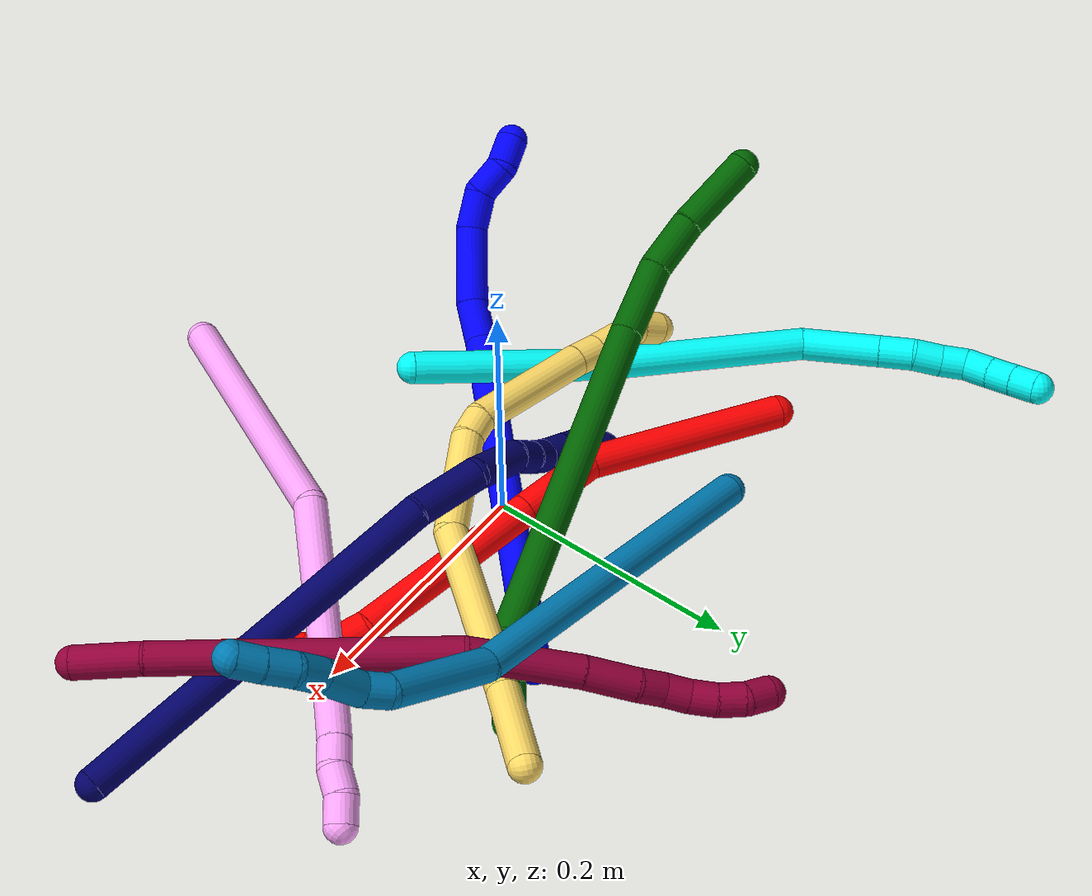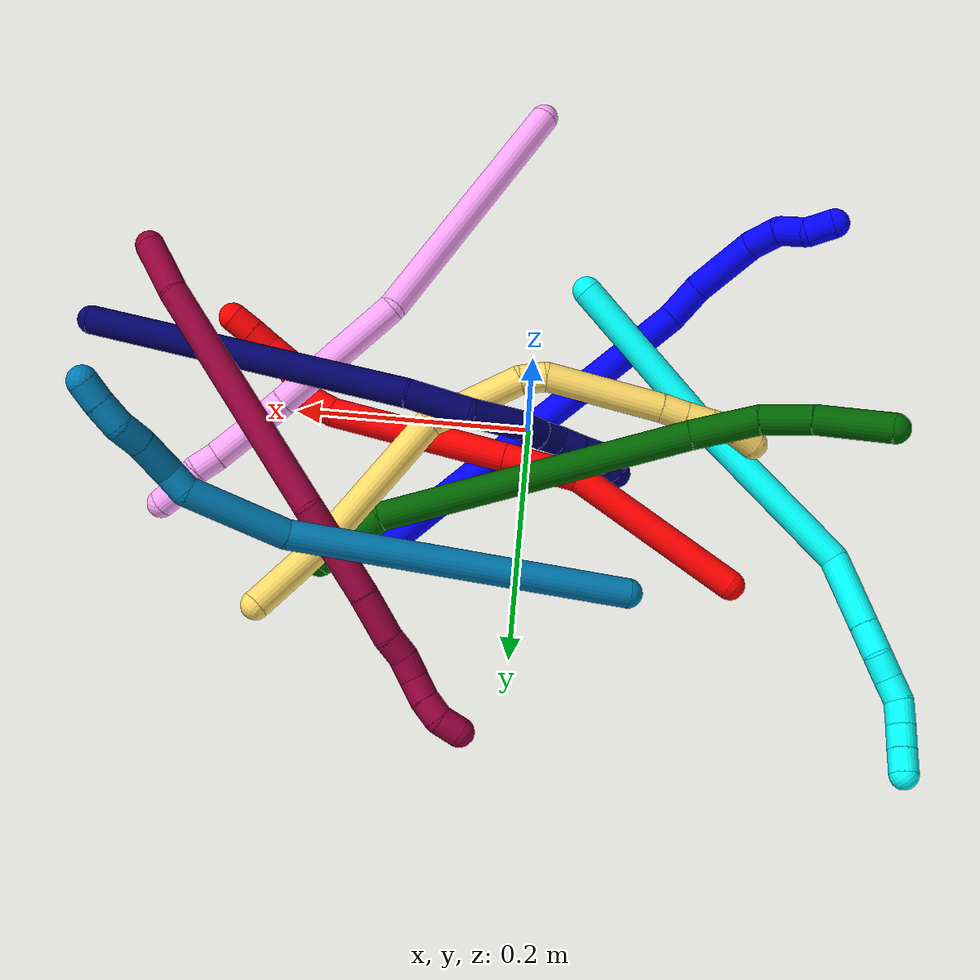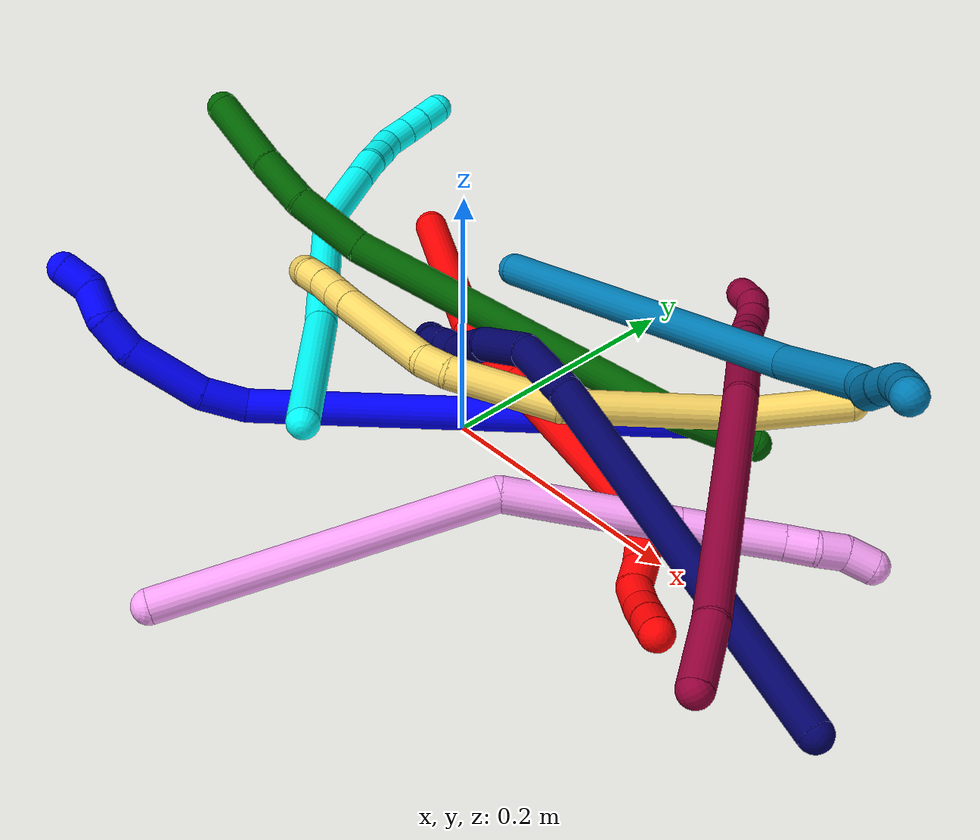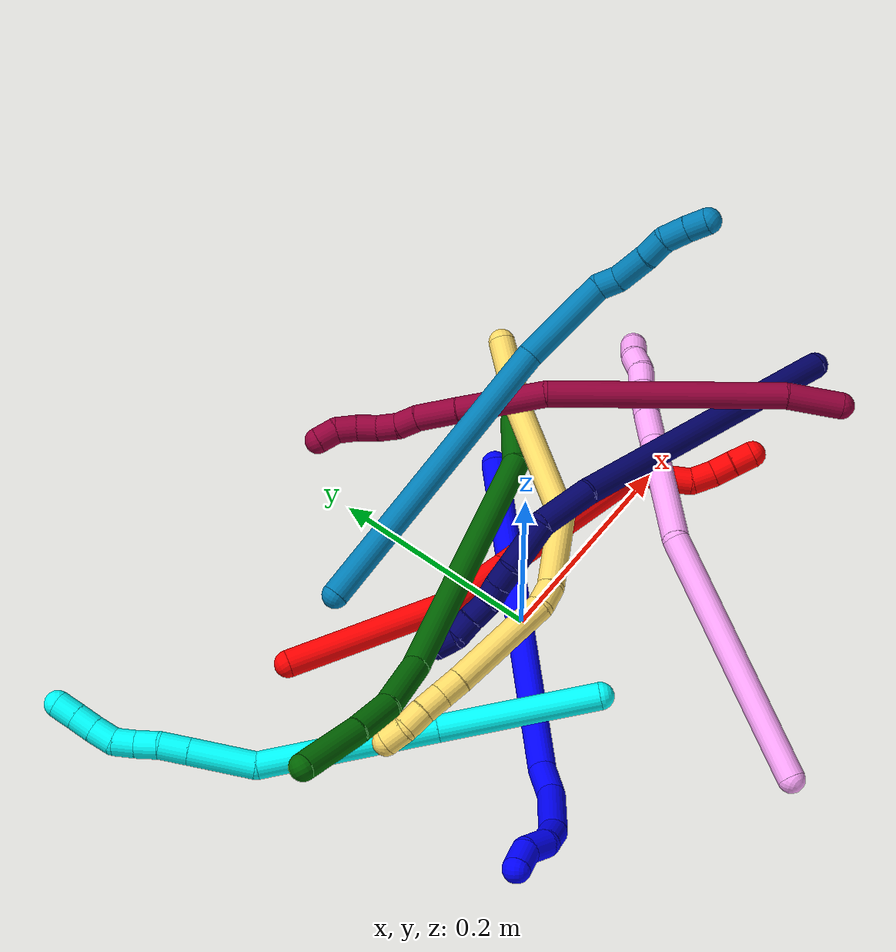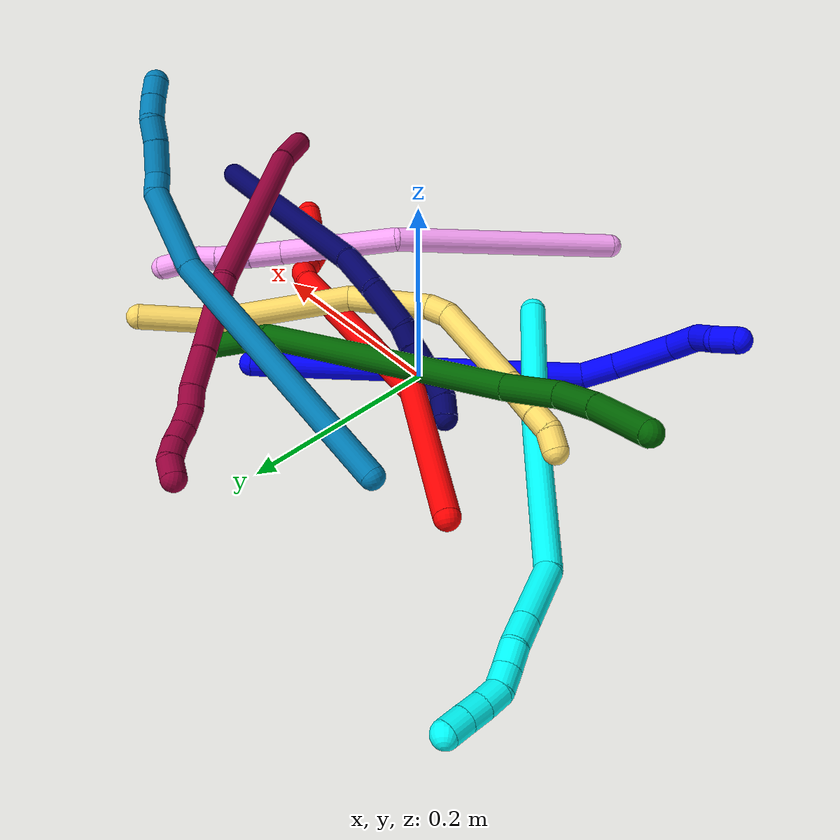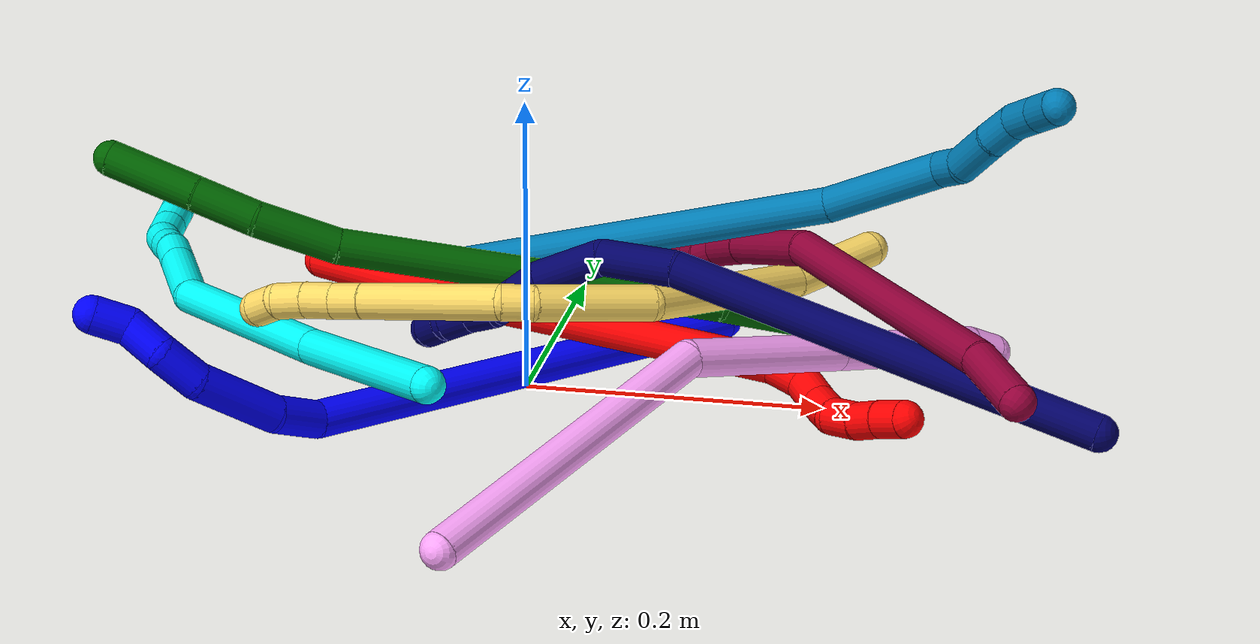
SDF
<sdf version="1.7">
 <world name="default">
  <plugin name="TubeGeneratorPlugin" filename="libtube_generator_plugin.so"/>
  <model name="photoneo_s_sensor">
   <static>1</static>
   <pose>0 0 2 1.57079 1.57079 3.14159</pose>
   <link name="link">
    <inertial><mass>0.1</mass></inertial>
    <sensor name="sensor" type="depth">
     <update_rate>30</update_rate>
     <camera>
      <horizontal_fov>1.22</horizontal_fov>
      <image><width>1920</width><height>1200</height><format>B8G8R8</format></image>
      <clip><near>0.1</near><far>4</far></clip>
      <depth_camera><output>points</output></depth_camera>
     </camera>
     <plugin name="camera_plugin" filename="libgazebo_ros_depth_camera.so">
      <baseline>0.2</baseline>
      <alwaysOn>1</alwaysOn>
      <updateRate>0.0</updateRate>
      <cameraName>camera_ir</cameraName>
      <imageTopicName>/camera/color/image_raw</imageTopicName>
      <cameraInfoTopicName>/camera/color/camera_info</cameraInfoTopicName>
      <depthImageTopicName>/camera/depth/image_raw</depthImageTopicName>
      <depthImageCameraInfoTopicName>/camera/depth/camera_info</depthImageCameraInfoTopicName>
      <pointCloudTopicName>/camera/depth/points</pointCloudTopicName>
      <frameName>fr_optical</frameName>
      <pointCloudCutoff>0.1</pointCloudCutoff>
      <pointCloudCutoffMax>2.0</pointCloudCutoffMax>
      <distortionK1>0</distortionK1>
      <distortionK2>0</distortionK2>
      <distortionK3>0</distortionK3>
      <distortionT1>0</distortionT1>
      <distortionT2>0</distortionT2>
      <CxPrime>0</CxPrime>
      <Cx>0</Cx>
      <Cy>0</Cy>
      <focalLength>0</focalLength>
      <hackBaseline>0</hackBaseline>
     </plugin>
    </sensor>
   </link>
  </model>
  <gravity>0 0 -9.8</gravity>
  <magnetic_field>6e-06 2.3e-05 -4.2e-05</magnetic_field>
  <atmosphere type="adiabatic"/>
  <physics name="default_physics" default="0" type="ode">
   <max_step_size>0.003</max_step_size>
   <real_time_factor>1</real_time_factor>
   <real_time_update_rate>1000</real_time_update_rate>
   <max_contacts>10000</max_contacts>
   <ode>
    <solver>
     <type>quick</type>
     <iters>100</iters>
     <sor>1.3</sor>
     <use_dynamic_moi_rescaling>0</use_dynamic_moi_rescaling>
    </solver>
    <constraints>
     <contact_max_correcting_vel>0</contact_max_correcting_vel>
     <contact_surface_layer>0.001</contact_surface_layer>
     <cfm>0</cfm>
     <erp>0.2</erp>
    </constraints>
   </ode>
  </physics>
  <scene><ambient>0.4 0.4 0.4 1</ambient><background>0.7 0.7 0.7 1</background><shadows>0</shadows></scene>
  <audio><device>default</device></audio>
  <spherical_coordinates>
   <surface_model>EARTH_WGS84</surface_model>
   <latitude_deg>0</latitude_deg>
   <longitude_deg>0</longitude_deg>
   <elevation>0</elevation>
   <heading_deg>0</heading_deg>
  </spherical_coordinates>
  <model name="bin">
   <static>1</static>
   <link name="bottom">
    <collision name="collision-bottom">
     <pose>0 0 -0.01 0 -0 0</pose>
     <geometry><box><size>0.8 0.6 0.02</size></box></geometry>
     <surface>
      <friction><ode><mu>100</mu><mu2>100</mu2></ode></friction>
      <contact><collide_bitmask>65535</collide_bitmask></contact>
     </surface>
    </collision>
   </link>
   <link name="west_wall">
    <collision name="collision-west_wall">
     <pose>-0.41 0 0.1 0 -0 0</pose>
     <geometry><box><size>0.02 0.6 0.2</size></box></geometry>
     <surface>
      <friction><ode><mu>100</mu><mu2>100</mu2></ode></friction>
      <contact><collide_bitmask>65535</collide_bitmask></contact>
     </surface>
    </collision>
   </link>
   <link name="east_wall">
    <collision name="collision-east_wall">
     <pose>0.41 0 0.1 0 -0 0</pose>
     <geometry><box><size>0.02 0.6 0.2</size></box></geometry>
     <surface>
      <friction><ode><mu>100</mu><mu2>100</mu2></ode></friction>
      <contact><collide_bitmask>65535</collide_bitmask></contact>
     </surface>
    </collision>
   </link>
   <link name="south_wall">
    <collision name="collision-south_wall">
     <pose>0 -0.31 0.1 0 -0 0</pose>
     <geometry><box><size>0.8 0.02 0.2</size></box></geometry>
     <surface>
      <friction><ode><mu>100</mu><mu2>100</mu2></ode></friction>
      <contact><collide_bitmask>65535</collide_bitmask></contact>
     </surface>
    </collision>
   </link>
   <link name="north_wall">
    <collision name="collision-north_wall">
     <pose>0 0.31 0.1 0 -0 0</pose>
     <geometry><box><size>0.8 0.02 0.2</size></box></geometry>
     <surface>
      <friction><ode><mu>100</mu><mu2>100</mu2></ode></friction>
      <contact><collide_bitmask>65535</collide_bitmask></contact>
     </surface>
    </collision>
   </link>
  </model>
  <model name="1">
   <static>0</static>
   <link name="1">
    <collision name="collision-cylinder-e_1_1_4">
     <pose>-0.103109 -0.102557 0.071631 0.961112 -0.689351 -0.370032</pose>
     <geometry><cylinder><radius>0.0125</radius><length>0.324224</length></cylinder></geometry>
     <surface>
      <friction><ode><mu>1.16</mu><mu2>1.16</mu2><slip1>0</slip1><slip2>0</slip2></ode></friction>
      <contact><ode><kp>1e+06</kp><kd>1</kd><max_vel>0</max_vel><min_depth>0.001</min_depth></ode></contact>
     </surface>
    </collision>
    <visual name="visual-cylinder-e_1_1_4">
     <pose>-0.103109 -0.102557 0.071631 0.961112 -0.689351 -0.370032</pose>
     <geometry><cylinder><radius>0.0125</radius><length>0.324224</length></cylinder></geometry>
     <material><ambient>0 0 1 1</ambient></material>
    </visual>
    <collision name="collision-cylinder-e_2_4_5">
     <pose>-0.218855 -0.21055 0.153871 0.473524 -0.814499 -0.207419</pose>
     <geometry><cylinder><radius>0.0125</radius><length>0.034744</length></cylinder></geometry>
     <surface>
      <friction><ode><mu>1.16</mu><mu2>1.16</mu2><slip1>0</slip1><slip2>0</slip2></ode></friction>
      <contact><ode><kp>1e+06</kp><kd>1</kd><max_vel>0</max_vel><min_depth>0.001</min_depth></ode></contact>
     </surface>
    </collision>
    <visual name="visual-cylinder-e_2_4_5">
     <pose>-0.218855 -0.21055 0.153871 0.473524 -0.814499 -0.207419</pose>
     <geometry><cylinder><radius>0.0125</radius><length>0.034744</length></cylinder></geometry>
     <material><ambient>0 0 1 1</ambient></material>
    </visual>
    <collision name="collision-cylinder-e_3_5_6">
     <pose>-0.257876 -0.219699 0.178747 0.254612 -1.06127 -0.14993</pose>
     <geometry><cylinder><radius>0.0125</radius><length>0.060449</length></cylinder></geometry>
     <surface>
      <friction><ode><mu>1.16</mu><mu2>1.16</mu2><slip1>0</slip1><slip2>0</slip2></ode></friction>
      <contact><ode><kp>1e+06</kp><kd>1</kd><max_vel>0</max_vel><min_depth>0.001</min_depth></ode></contact>
     </surface>
    </collision>
    <visual name="visual-cylinder-e_3_5_6">
     <pose>-0.257876 -0.219699 0.178747 0.254612 -1.06127 -0.14993</pose>
     <geometry><cylinder><radius>0.0125</radius><length>0.060449</length></cylinder></geometry>
     <material><ambient>0 0 1 1</ambient></material>
    </visual>
    <collision name="collision-cylinder-e_4_6_7">
     <pose>-0.29866 -0.221781 0.196983 -0.39005 -1.28113 0.292395</pose>
     <geometry><cylinder><radius>0.0125</radius><length>0.030049</length></cylinder></geometry>
     <surface>
      <friction><ode><mu>1.16</mu><mu2>1.16</mu2><slip1>0</slip1><slip2>0</slip2></ode></friction>
      <contact><ode><kp>1e+06</kp><kd>1</kd><max_vel>0</max_vel><min_depth>0.001</min_depth></ode></contact>
     </surface>
    </collision>
    <visual name="visual-cylinder-e_4_6_7">
     <pose>-0.29866 -0.221781 0.196983 -0.39005 -1.28113 0.292395</pose>
     <geometry><cylinder><radius>0.0125</radius><length>0.030049</length></cylinder></geometry>
     <material><ambient>0 0 1 1</ambient></material>
    </visual>
    <collision name="collision-cylinder-e_5_7_8">
     <pose>-0.32575 -0.218411 0.198278 -2.56547 -1.3246 2.41535</pose>
     <geometry><cylinder><radius>0.0125</radius><length>0.026172</length></cylinder></geometry>
     <surface>
      <friction><ode><mu>1.16</mu><mu2>1.16</mu2><slip1>0</slip1><slip2>0</slip2></ode></friction>
      <contact><ode><kp>1e+06</kp><kd>1</kd><max_vel>0</max_vel><min_depth>0.001</min_depth></ode></contact>
     </surface>
    </collision>
    <visual name="visual-cylinder-e_5_7_8">
     <pose>-0.32575 -0.218411 0.198278 -2.56547 -1.3246 2.41535</pose>
     <geometry><cylinder><radius>0.0125</radius><length>0.026172</length></cylinder></geometry>
     <material><ambient>0 0 1 1</ambient></material>
    </visual>
    <collision name="collision-cylinder-e_6_8_2">
     <pose>-0.350124 -0.219725 0.197213 1.08536 -1.2837 -0.846969</pose>
     <geometry><cylinder><radius>0.0125</radius><length>0.024362</length></cylinder></geometry>
     <surface>
      <friction><ode><mu>1.16</mu><mu2>1.16</mu2><slip1>0</slip1><slip2>0</slip2></ode></friction>
      <contact><ode><kp>1e+06</kp><kd>1</kd><max_vel>0</max_vel><min_depth>0.001</min_depth></ode></contact>
     </surface>
    </collision>
    <visual name="visual-cylinder-e_6_8_2">
     <pose>-0.350124 -0.219725 0.197213 1.08536 -1.2837 -0.846969</pose>
     <geometry><cylinder><radius>0.0125</radius><length>0.024362</length></cylinder></geometry>
     <material><ambient>0 0 1 1</ambient></material>
    </visual>
    <collision name="collision-sphere-2">
     <pose>-0.361806 -0.222775 0.198822 0 -0 0</pose>
     <geometry><sphere><radius>0.0125</radius></sphere></geometry>
     <surface>
      <friction><ode><mu>1.16</mu><mu2>1.16</mu2><slip1>0</slip1><slip2>0</slip2></ode></friction>
      <contact><ode><kp>1e+06</kp><kd>1</kd><max_vel>0</max_vel><min_depth>0.001</min_depth></ode></contact>
     </surface>
    </collision>
    <visual name="visual-sphere-2">
     <pose>-0.361806 -0.222775 0.198822 0 -0 0</pose>
     <geometry><sphere><radius>0.0125</radius></sphere></geometry>
     <material><ambient>0 0 1 1</ambient></material>
    </visual>
    <collision name="collision-sphere-4">
     <pose>-0.206219 -0.205113 0.143261 0 -0 0</pose>
     <geometry><sphere><radius>0.0125</radius></sphere></geometry>
     <surface>
      <friction><ode><mu>1.16</mu><mu2>1.16</mu2><slip1>0</slip1><slip2>0</slip2></ode></friction>
      <contact><ode><kp>1e+06</kp><kd>1</kd><max_vel>0</max_vel><min_depth>0.001</min_depth></ode></contact>
     </surface>
    </collision>
    <visual name="visual-sphere-4">
     <pose>-0.206219 -0.205113 0.143261 0 -0 0</pose>
     <geometry><sphere><radius>0.0125</radius></sphere></geometry>
     <material><ambient>0 0 1 1</ambient></material>
    </visual>
    <collision name="collision-sphere-1">
     <geometry><sphere><radius>0.0125</radius></sphere></geometry>
     <surface>
      <friction><ode><mu>1.16</mu><mu2>1.16</mu2><slip1>0</slip1><slip2>0</slip2></ode></friction>
      <contact><ode><kp>1e+06</kp><kd>1</kd><max_vel>0</max_vel><min_depth>0.001</min_depth></ode></contact>
     </surface>
    </collision>
    <visual name="visual-sphere-1">
     <geometry><sphere><radius>0.0125</radius></sphere></geometry>
     <material><ambient>0 0 1 1</ambient></material>
    </visual>
    <collision name="collision-sphere-8">
     <pose>-0.338441 -0.216674 0.195604 0 -0 0</pose>
     <geometry><sphere><radius>0.0125</radius></sphere></geometry>
     <surface>
      <friction><ode><mu>1.16</mu><mu2>1.16</mu2><slip1>0</slip1><slip2>0</slip2></ode></friction>
      <contact><ode><kp>1e+06</kp><kd>1</kd><max_vel>0</max_vel><min_depth>0.001</min_depth></ode></contact>
     </surface>
    </collision>
    <visual name="visual-sphere-8">
     <pose>-0.338441 -0.216674 0.195604 0 -0 0</pose>
     <geometry><sphere><radius>0.0125</radius></sphere></geometry>
     <material><ambient>0 0 1 1</ambient></material>
    </visual>
    <collision name="collision-sphere-5">
     <pose>-0.23149 -0.215986 0.16448 0 -0 0</pose>
     <geometry><sphere><radius>0.0125</radius></sphere></geometry>
     <surface>
      <friction><ode><mu>1.16</mu><mu2>1.16</mu2><slip1>0</slip1><slip2>0</slip2></ode></friction>
      <contact><ode><kp>1e+06</kp><kd>1</kd><max_vel>0</max_vel><min_depth>0.001</min_depth></ode></contact>
     </surface>
    </collision>
    <visual name="visual-sphere-5">
     <pose>-0.23149 -0.215986 0.16448 0 -0 0</pose>
     <geometry><sphere><radius>0.0125</radius></sphere></geometry>
     <material><ambient>0 0 1 1</ambient></material>
    </visual>
    <collision name="collision-sphere-6">
     <pose>-0.284261 -0.223412 0.193014 0 -0 0</pose>
     <geometry><sphere><radius>0.0125</radius></sphere></geometry>
     <surface>
      <friction><ode><mu>1.16</mu><mu2>1.16</mu2><slip1>0</slip1><slip2>0</slip2></ode></friction>
      <contact><ode><kp>1e+06</kp><kd>1</kd><max_vel>0</max_vel><min_depth>0.001</min_depth></ode></contact>
     </surface>
    </collision>
    <visual name="visual-sphere-6">
     <pose>-0.284261 -0.223412 0.193014 0 -0 0</pose>
     <geometry><sphere><radius>0.0125</radius></sphere></geometry>
     <material><ambient>0 0 1 1</ambient></material>
    </visual>
    <collision name="collision-sphere-7">
     <pose>-0.313058 -0.220149 0.200952 0 -0 0</pose>
     <geometry><sphere><radius>0.0125</radius></sphere></geometry>
     <surface>
      <friction><ode><mu>1.16</mu><mu2>1.16</mu2><slip1>0</slip1><slip2>0</slip2></ode></friction>
      <contact><ode><kp>1e+06</kp><kd>1</kd><max_vel>0</max_vel><min_depth>0.001</min_depth></ode></contact>
     </surface>
    </collision>
    <visual name="visual-sphere-7">
     <pose>-0.313058 -0.220149 0.200952 0 -0 0</pose>
     <geometry><sphere><radius>0.0125</radius></sphere></geometry>
     <material><ambient>0 0 1 1</ambient></material>
    </visual>
    <inertial>
     <pose>-0.165305 -0.143161 0.110577 0 -0 0</pose>
     <mass>0.5</mass>
     <inertia>
      <ixx>0.00124</ixx>
      <ixy>0</ixy>
      <ixz>0</ixz>
      <iyy>0.001279</iyy>
      <iyz>0</iyz>
      <izz>0.003668</izz>
     </inertia>
    </inertial>
   </link>
   <pose>0.115462 0.117802 0.011497 1.14411 0.553497 0.050867</pose>
  </model>
  <model name="2">
   <static>0</static>
   <link name="2">
    <collision name="collision-cylinder-e_1_1_4">
     <pose>0.026012 -0.022038 0.069021 0.309059 0.344683 0.054216</pose>
     <geometry><cylinder><radius>0.0125</radius><length>0.153964</length></cylinder></geometry>
     <surface>
      <friction><ode><mu>1.16</mu><mu2>1.16</mu2><slip1>0</slip1><slip2>0</slip2></ode></friction>
      <contact><ode><kp>1e+06</kp><kd>1</kd><max_vel>0</max_vel><min_depth>0.001</min_depth></ode></contact>
     </surface>
    </collision>
    <visual name="visual-cylinder-e_1_1_4">
     <pose>0.026012 -0.022038 0.069021 0.309059 0.344683 0.054216</pose>
     <geometry><cylinder><radius>0.0125</radius><length>0.153964</length></cylinder></geometry>
     <material><ambient>1 0 0 1</ambient></material>
    </visual>
    <collision name="collision-cylinder-e_2_4_5">
     <pose>0.071342 -0.04641 0.163694 0.090748 0.643478 0.030267</pose>
     <geometry><cylinder><radius>0.0125</radius><length>0.064394</length></cylinder></geometry>
     <surface>
      <friction><ode><mu>1.16</mu><mu2>1.16</mu2><slip1>0</slip1><slip2>0</slip2></ode></friction>
      <contact><ode><kp>1e+06</kp><kd>1</kd><max_vel>0</max_vel><min_depth>0.001</min_depth></ode></contact>
     </surface>
    </collision>
    <visual name="visual-cylinder-e_2_4_5">
     <pose>0.071342 -0.04641 0.163694 0.090748 0.643478 0.030267</pose>
     <geometry><cylinder><radius>0.0125</radius><length>0.064394</length></cylinder></geometry>
     <material><ambient>1 0 0 1</ambient></material>
    </visual>
    <collision name="collision-cylinder-e_3_5_6">
     <pose>0.136971 -0.054168 0.249403 0.090072 0.654928 0.030615</pose>
     <geometry><cylinder><radius>0.0125</radius><length>0.152067</length></cylinder></geometry>
     <surface>
      <friction><ode><mu>1.16</mu><mu2>1.16</mu2><slip1>0</slip1><slip2>0</slip2></ode></friction>
      <contact><ode><kp>1e+06</kp><kd>1</kd><max_vel>0</max_vel><min_depth>0.001</min_depth></ode></contact>
     </surface>
    </collision>
    <visual name="visual-cylinder-e_3_5_6">
     <pose>0.136971 -0.054168 0.249403 0.090072 0.654928 0.030615</pose>
     <geometry><cylinder><radius>0.0125</radius><length>0.152067</length></cylinder></geometry>
     <material><ambient>1 0 0 1</ambient></material>
    </visual>
    <collision name="collision-cylinder-e_4_6_7">
     <pose>0.190024 -0.064096 0.318446 0.464582 0.590758 0.143714</pose>
     <geometry><cylinder><radius>0.0125</radius><length>0.024205</length></cylinder></geometry>
     <surface>
      <friction><ode><mu>1.16</mu><mu2>1.16</mu2><slip1>0</slip1><slip2>0</slip2></ode></friction>
      <contact><ode><kp>1e+06</kp><kd>1</kd><max_vel>0</max_vel><min_depth>0.001</min_depth></ode></contact>
     </surface>
    </collision>
    <visual name="visual-cylinder-e_4_6_7">
     <pose>0.190024 -0.064096 0.318446 0.464582 0.590758 0.143714</pose>
     <geometry><cylinder><radius>0.0125</radius><length>0.024205</length></cylinder></geometry>
     <material><ambient>1 0 0 1</ambient></material>
    </visual>
    <collision name="collision-cylinder-e_5_7_8">
     <pose>0.200388 -0.076522 0.334167 0.866286 0.335255 0.156182</pose>
     <geometry><cylinder><radius>0.0125</radius><length>0.022021</length></cylinder></geometry>
     <surface>
      <friction><ode><mu>1.16</mu><mu2>1.16</mu2><slip1>0</slip1><slip2>0</slip2></ode></friction>
      <contact><ode><kp>1e+06</kp><kd>1</kd><max_vel>0</max_vel><min_depth>0.001</min_depth></ode></contact>
     </surface>
    </collision>
    <visual name="visual-cylinder-e_5_7_8">
     <pose>0.200388 -0.076522 0.334167 0.866286 0.335255 0.156182</pose>
     <geometry><cylinder><radius>0.0125</radius><length>0.022021</length></cylinder></geometry>
     <material><ambient>1 0 0 1</ambient></material>
    </visual>
    <collision name="collision-cylinder-e_6_8_9">
     <pose>0.205134 -0.091617 0.348557 0.75278 0.106713 0.04221</pose>
     <geometry><cylinder><radius>0.0125</radius><length>0.021103</length></cylinder></geometry>
     <surface>
      <friction><ode><mu>1.16</mu><mu2>1.16</mu2><slip1>0</slip1><slip2>0</slip2></ode></friction>
      <contact><ode><kp>1e+06</kp><kd>1</kd><max_vel>0</max_vel><min_depth>0.001</min_depth></ode></contact>
     </surface>
    </collision>
    <visual name="visual-cylinder-e_6_8_9">
     <pose>0.205134 -0.091617 0.348557 0.75278 0.106713 0.04221</pose>
     <geometry><cylinder><radius>0.0125</radius><length>0.021103</length></cylinder></geometry>
     <material><ambient>1 0 0 1</ambient></material>
    </visual>
    <collision name="collision-cylinder-e_7_9_10">
     <pose>0.208997 -0.10191 0.366381 0.297818 0.252029 0.038006</pose>
     <geometry><cylinder><radius>0.0125</radius><length>0.021965</length></cylinder></geometry>
     <surface>
      <friction><ode><mu>1.16</mu><mu2>1.16</mu2><slip1>0</slip1><slip2>0</slip2></ode></friction>
      <contact><ode><kp>1e+06</kp><kd>1</kd><max_vel>0</max_vel><min_depth>0.001</min_depth></ode></contact>
     </surface>
    </collision>
    <visual name="visual-cylinder-e_7_9_10">
     <pose>0.208997 -0.10191 0.366381 0.297818 0.252029 0.038006</pose>
     <geometry><cylinder><radius>0.0125</radius><length>0.021965</length></cylinder></geometry>
     <material><ambient>1 0 0 1</ambient></material>
    </visual>
    <collision name="collision-cylinder-e_8_10_11">
     <pose>0.212704 -0.106407 0.38647 0.137835 0.096401 0.006659</pose>
     <geometry><cylinder><radius>0.0125</radius><length>0.020127</length></cylinder></geometry>
     <surface>
      <friction><ode><mu>1.16</mu><mu2>1.16</mu2><slip1>0</slip1><slip2>0</slip2></ode></friction>
      <contact><ode><kp>1e+06</kp><kd>1</kd><max_vel>0</max_vel><min_depth>0.001</min_depth></ode></contact>
     </surface>
    </collision>
    <visual name="visual-cylinder-e_8_10_11">
     <pose>0.212704 -0.106407 0.38647 0.137835 0.096401 0.006659</pose>
     <geometry><cylinder><radius>0.0125</radius><length>0.020127</length></cylinder></geometry>
     <material><ambient>1 0 0 1</ambient></material>
    </visual>
    <collision name="collision-cylinder-e_9_11_2">
     <pose>0.215347 -0.109357 0.406204 0.159008 0.16694 0.013331</pose>
     <geometry><cylinder><radius>0.0125</radius><length>0.020154</length></cylinder></geometry>
     <surface>
      <friction><ode><mu>1.16</mu><mu2>1.16</mu2><slip1>0</slip1><slip2>0</slip2></ode></friction>
      <contact><ode><kp>1e+06</kp><kd>1</kd><max_vel>0</max_vel><min_depth>0.001</min_depth></ode></contact>
     </surface>
    </collision>
    <visual name="visual-cylinder-e_9_11_2">
     <pose>0.215347 -0.109357 0.406204 0.159008 0.16694 0.013331</pose>
     <geometry><cylinder><radius>0.0125</radius><length>0.020154</length></cylinder></geometry>
     <material><ambient>1 0 0 1</ambient></material>
    </visual>
    <collision name="collision-sphere-2">
     <pose>0.217022 -0.11093 0.416016 0 -0 0</pose>
     <geometry><sphere><radius>0.0125</radius></sphere></geometry>
     <surface>
      <friction><ode><mu>1.16</mu><mu2>1.16</mu2><slip1>0</slip1><slip2>0</slip2></ode></friction>
      <contact><ode><kp>1e+06</kp><kd>1</kd><max_vel>0</max_vel><min_depth>0.001</min_depth></ode></contact>
     </surface>
    </collision>
    <visual name="visual-sphere-2">
     <pose>0.217022 -0.11093 0.416016 0 -0 0</pose>
     <geometry><sphere><radius>0.0125</radius></sphere></geometry>
     <material><ambient>1 0 0 1</ambient></material>
    </visual>
    <collision name="collision-sphere-11">
     <pose>0.213673 -0.107784 0.396392 0 -0 0</pose>
     <geometry><sphere><radius>0.0125</radius></sphere></geometry>
     <surface>
      <friction><ode><mu>1.16</mu><mu2>1.16</mu2><slip1>0</slip1><slip2>0</slip2></ode></friction>
      <contact><ode><kp>1e+06</kp><kd>1</kd><max_vel>0</max_vel><min_depth>0.001</min_depth></ode></contact>
     </surface>
    </collision>
    <visual name="visual-sphere-11">
     <pose>0.213673 -0.107784 0.396392 0 -0 0</pose>
     <geometry><sphere><radius>0.0125</radius></sphere></geometry>
     <material><ambient>1 0 0 1</ambient></material>
    </visual>
    <collision name="collision-sphere-10">
     <pose>0.211736 -0.105031 0.376548 0 -0 0</pose>
     <geometry><sphere><radius>0.0125</radius></sphere></geometry>
     <surface>
      <friction><ode><mu>1.16</mu><mu2>1.16</mu2><slip1>0</slip1><slip2>0</slip2></ode></friction>
      <contact><ode><kp>1e+06</kp><kd>1</kd><max_vel>0</max_vel><min_depth>0.001</min_depth></ode></contact>
     </surface>
    </collision>
    <visual name="visual-sphere-10">
     <pose>0.211736 -0.105031 0.376548 0 -0 0</pose>
     <geometry><sphere><radius>0.0125</radius></sphere></geometry>
     <material><ambient>1 0 0 1</ambient></material>
    </visual>
    <collision name="collision-sphere-9">
     <pose>0.206258 -0.098789 0.356214 0 -0 0</pose>
     <geometry><sphere><radius>0.0125</radius></sphere></geometry>
     <surface>
      <friction><ode><mu>1.16</mu><mu2>1.16</mu2><slip1>0</slip1><slip2>0</slip2></ode></friction>
      <contact><ode><kp>1e+06</kp><kd>1</kd><max_vel>0</max_vel><min_depth>0.001</min_depth></ode></contact>
     </surface>
    </collision>
    <visual name="visual-sphere-9">
     <pose>0.206258 -0.098789 0.356214 0 -0 0</pose>
     <geometry><sphere><radius>0.0125</radius></sphere></geometry>
     <material><ambient>1 0 0 1</ambient></material>
    </visual>
    <collision name="collision-sphere-4">
     <pose>0.052024 -0.044076 0.138042 0 -0 0</pose>
     <geometry><sphere><radius>0.0125</radius></sphere></geometry>
     <surface>
      <friction><ode><mu>1.16</mu><mu2>1.16</mu2><slip1>0</slip1><slip2>0</slip2></ode></friction>
      <contact><ode><kp>1e+06</kp><kd>1</kd><max_vel>0</max_vel><min_depth>0.001</min_depth></ode></contact>
     </surface>
    </collision>
    <visual name="visual-sphere-4">
     <pose>0.052024 -0.044076 0.138042 0 -0 0</pose>
     <geometry><sphere><radius>0.0125</radius></sphere></geometry>
     <material><ambient>1 0 0 1</ambient></material>
    </visual>
    <collision name="collision-sphere-1">
     <geometry><sphere><radius>0.0125</radius></sphere></geometry>
     <surface>
      <friction><ode><mu>1.16</mu><mu2>1.16</mu2><slip1>0</slip1><slip2>0</slip2></ode></friction>
      <contact><ode><kp>1e+06</kp><kd>1</kd><max_vel>0</max_vel><min_depth>0.001</min_depth></ode></contact>
     </surface>
    </collision>
    <visual name="visual-sphere-1">
     <geometry><sphere><radius>0.0125</radius></sphere></geometry>
     <material><ambient>1 0 0 1</ambient></material>
    </visual>
    <collision name="collision-sphere-8">
     <pose>0.204011 -0.084444 0.340901 0 -0 0</pose>
     <geometry><sphere><radius>0.0125</radius></sphere></geometry>
     <surface>
      <friction><ode><mu>1.16</mu><mu2>1.16</mu2><slip1>0</slip1><slip2>0</slip2></ode></friction>
      <contact><ode><kp>1e+06</kp><kd>1</kd><max_vel>0</max_vel><min_depth>0.001</min_depth></ode></contact>
     </surface>
    </collision>
    <visual name="visual-sphere-8">
     <pose>0.204011 -0.084444 0.340901 0 -0 0</pose>
     <geometry><sphere><radius>0.0125</radius></sphere></geometry>
     <material><ambient>1 0 0 1</ambient></material>
    </visual>
    <collision name="collision-sphere-5">
     <pose>0.090659 -0.048744 0.189346 0 -0 0</pose>
     <geometry><sphere><radius>0.0125</radius></sphere></geometry>
     <surface>
      <friction><ode><mu>1.16</mu><mu2>1.16</mu2><slip1>0</slip1><slip2>0</slip2></ode></friction>
      <contact><ode><kp>1e+06</kp><kd>1</kd><max_vel>0</max_vel><min_depth>0.001</min_depth></ode></contact>
     </surface>
    </collision>
    <visual name="visual-sphere-5">
     <pose>0.090659 -0.048744 0.189346 0 -0 0</pose>
     <geometry><sphere><radius>0.0125</radius></sphere></geometry>
     <material><ambient>1 0 0 1</ambient></material>
    </visual>
    <collision name="collision-sphere-6">
     <pose>0.183283 -0.059592 0.30946 0 -0 0</pose>
     <geometry><sphere><radius>0.0125</radius></sphere></geometry>
     <surface>
      <friction><ode><mu>1.16</mu><mu2>1.16</mu2><slip1>0</slip1><slip2>0</slip2></ode></friction>
      <contact><ode><kp>1e+06</kp><kd>1</kd><max_vel>0</max_vel><min_depth>0.001</min_depth></ode></contact>
     </surface>
    </collision>
    <visual name="visual-sphere-6">
     <pose>0.183283 -0.059592 0.30946 0 -0 0</pose>
     <geometry><sphere><radius>0.0125</radius></sphere></geometry>
     <material><ambient>1 0 0 1</ambient></material>
    </visual>
    <collision name="collision-sphere-7">
     <pose>0.196766 -0.0686 0.327433 0 -0 0</pose>
     <geometry><sphere><radius>0.0125</radius></sphere></geometry>
     <surface>
      <friction><ode><mu>1.16</mu><mu2>1.16</mu2><slip1>0</slip1><slip2>0</slip2></ode></friction>
      <contact><ode><kp>1e+06</kp><kd>1</kd><max_vel>0</max_vel><min_depth>0.001</min_depth></ode></contact>
     </surface>
    </collision>
    <visual name="visual-sphere-7">
     <pose>0.196766 -0.0686 0.327433 0 -0 0</pose>
     <geometry><sphere><radius>0.0125</radius></sphere></geometry>
     <material><ambient>1 0 0 1</ambient></material>
    </visual>
    <inertial>
     <pose>0.111962 -0.052746 0.211058 0 -0 0</pose>
     <mass>0.5</mass>
     <inertia>
      <ixx>0.000599</ixx>
      <ixy>0</ixy>
      <ixz>0</ixz>
      <iyy>0.000644</iyy>
      <iyz>0</iyz>
      <izz>-0.000156</izz>
     </inertia>
    </inertial>
   </link>
   <pose>-0.177304 0.127289 0.032581 0.840069 0.752347 0.495847</pose>
  </model>
  <model name="3">
   <static>0</static>
   <link name="3">
    <collision name="collision-cylinder-e_1_1_4">
     <pose>0.000209 -0.001798 0.072983 0.024633 0.002867 3.5e-05</pose>
     <geometry><cylinder><radius>0.0125</radius><length>0.146011</length></cylinder></geometry>
     <surface>
      <friction><ode><mu>1.16</mu><mu2>1.16</mu2><slip1>0</slip1><slip2>0</slip2></ode></friction>
      <contact><ode><kp>1e+06</kp><kd>1</kd><max_vel>0</max_vel><min_depth>0.001</min_depth></ode></contact>
     </surface>
    </collision>
    <visual name="visual-cylinder-e_1_1_4">
     <pose>0.000209 -0.001798 0.072983 0.024633 0.002867 3.5e-05</pose>
     <geometry><cylinder><radius>0.0125</radius><length>0.146011</length></cylinder></geometry>
     <material><ambient>0.003922 1 0.996078 1</ambient></material>
    </visual>
    <collision name="collision-cylinder-e_2_4_5">
     <pose>0.006374 -0.001584 0.227092 -0.024794 0.073257 -0.000909</pose>
     <geometry><cylinder><radius>0.0125</radius><length>0.162738</length></cylinder></geometry>
     <surface>
      <friction><ode><mu>1.16</mu><mu2>1.16</mu2><slip1>0</slip1><slip2>0</slip2></ode></friction>
      <contact><ode><kp>1e+06</kp><kd>1</kd><max_vel>0</max_vel><min_depth>0.001</min_depth></ode></contact>
     </surface>
    </collision>
    <visual name="visual-cylinder-e_2_4_5">
     <pose>0.006374 -0.001584 0.227092 -0.024794 0.073257 -0.000909</pose>
     <geometry><cylinder><radius>0.0125</radius><length>0.162738</length></cylinder></geometry>
     <material><ambient>0.003922 1 0.996078 1</ambient></material>
    </visual>
    <collision name="collision-cylinder-e_3_5_6">
     <pose>0.005232 0.009279 0.336535 -0.302951 -0.234828 0.036007</pose>
     <geometry><cylinder><radius>0.0125</radius><length>0.061012</length></cylinder></geometry>
     <surface>
      <friction><ode><mu>1.16</mu><mu2>1.16</mu2><slip1>0</slip1><slip2>0</slip2></ode></friction>
      <contact><ode><kp>1e+06</kp><kd>1</kd><max_vel>0</max_vel><min_depth>0.001</min_depth></ode></contact>
     </surface>
    </collision>
    <visual name="visual-cylinder-e_3_5_6">
     <pose>0.005232 0.009279 0.336535 -0.302951 -0.234828 0.036007</pose>
     <geometry><cylinder><radius>0.0125</radius><length>0.061012</length></cylinder></geometry>
     <material><ambient>0.003922 1 0.996078 1</ambient></material>
    </visual>
    <collision name="collision-cylinder-e_4_6_7">
     <pose>-0.004971 0.021889 0.377201 -0.295496 -0.23606 0.035294</pose>
     <geometry><cylinder><radius>0.0125</radius><length>0.026551</length></cylinder></geometry>
     <surface>
      <friction><ode><mu>1.16</mu><mu2>1.16</mu2><slip1>0</slip1><slip2>0</slip2></ode></friction>
      <contact><ode><kp>1e+06</kp><kd>1</kd><max_vel>0</max_vel><min_depth>0.001</min_depth></ode></contact>
     </surface>
    </collision>
    <visual name="visual-cylinder-e_4_6_7">
     <pose>-0.004971 0.021889 0.377201 -0.295496 -0.23606 0.035294</pose>
     <geometry><cylinder><radius>0.0125</radius><length>0.026551</length></cylinder></geometry>
     <material><ambient>0.003922 1 0.996078 1</ambient></material>
    </visual>
    <collision name="collision-cylinder-e_5_7_8">
     <pose>-0.011036 0.026255 0.399893 -0.058655 -0.278266 0.008216</pose>
     <geometry><cylinder><radius>0.0125</radius><length>0.021553</length></cylinder></geometry>
     <surface>
      <friction><ode><mu>1.16</mu><mu2>1.16</mu2><slip1>0</slip1><slip2>0</slip2></ode></friction>
      <contact><ode><kp>1e+06</kp><kd>1</kd><max_vel>0</max_vel><min_depth>0.001</min_depth></ode></contact>
     </surface>
    </collision>
    <visual name="visual-cylinder-e_5_7_8">
     <pose>-0.011036 0.026255 0.399893 -0.058655 -0.278266 0.008216</pose>
     <geometry><cylinder><radius>0.0125</radius><length>0.021553</length></cylinder></geometry>
     <material><ambient>0.003922 1 0.996078 1</ambient></material>
    </visual>
    <collision name="collision-cylinder-e_6_8_9">
     <pose>-0.016438 0.028509 0.419985 -0.167293 -0.242179 0.020404</pose>
     <geometry><cylinder><radius>0.0125</radius><length>0.020368</length></cylinder></geometry>
     <surface>
      <friction><ode><mu>1.16</mu><mu2>1.16</mu2><slip1>0</slip1><slip2>0</slip2></ode></friction>
      <contact><ode><kp>1e+06</kp><kd>1</kd><max_vel>0</max_vel><min_depth>0.001</min_depth></ode></contact>
     </surface>
    </collision>
    <visual name="visual-cylinder-e_6_8_9">
     <pose>-0.016438 0.028509 0.419985 -0.167293 -0.242179 0.020404</pose>
     <geometry><cylinder><radius>0.0125</radius><length>0.020368</length></cylinder></geometry>
     <material><ambient>0.003922 1 0.996078 1</ambient></material>
    </visual>
    <collision name="collision-cylinder-e_7_9_10">
     <pose>-0.024339 0.034706 0.437724 -0.517794 -0.53568 0.145107</pose>
     <geometry><cylinder><radius>0.0125</radius><length>0.021385</length></cylinder></geometry>
     <surface>
      <friction><ode><mu>1.16</mu><mu2>1.16</mu2><slip1>0</slip1><slip2>0</slip2></ode></friction>
      <contact><ode><kp>1e+06</kp><kd>1</kd><max_vel>0</max_vel><min_depth>0.001</min_depth></ode></contact>
     </surface>
    </collision>
    <visual name="visual-cylinder-e_7_9_10">
     <pose>-0.024339 0.034706 0.437724 -0.517794 -0.53568 0.145107</pose>
     <geometry><cylinder><radius>0.0125</radius><length>0.021385</length></cylinder></geometry>
     <material><ambient>0.003922 1 0.996078 1</ambient></material>
    </visual>
    <collision name="collision-cylinder-e_8_10_11">
     <pose>-0.034874 0.044125 0.452839 -0.599276 -0.53186 0.167903</pose>
     <geometry><cylinder><radius>0.0125</radius><length>0.020025</length></cylinder></geometry>
     <surface>
      <friction><ode><mu>1.16</mu><mu2>1.16</mu2><slip1>0</slip1><slip2>0</slip2></ode></friction>
      <contact><ode><kp>1e+06</kp><kd>1</kd><max_vel>0</max_vel><min_depth>0.001</min_depth></ode></contact>
     </surface>
    </collision>
    <visual name="visual-cylinder-e_8_10_11">
     <pose>-0.034874 0.044125 0.452839 -0.599276 -0.53186 0.167903</pose>
     <geometry><cylinder><radius>0.0125</radius><length>0.020025</length></cylinder></geometry>
     <material><ambient>0.003922 1 0.996078 1</ambient></material>
    </visual>
    <collision name="collision-cylinder-e_9_11_2">
     <pose>-0.045045 0.053855 0.467314 -0.584526 -0.524061 0.161041</pose>
     <geometry><cylinder><radius>0.0125</radius><length>0.020357</length></cylinder></geometry>
     <surface>
      <friction><ode><mu>1.16</mu><mu2>1.16</mu2><slip1>0</slip1><slip2>0</slip2></ode></friction>
      <contact><ode><kp>1e+06</kp><kd>1</kd><max_vel>0</max_vel><min_depth>0.001</min_depth></ode></contact>
     </surface>
    </collision>
    <visual name="visual-cylinder-e_9_11_2">
     <pose>-0.045045 0.053855 0.467314 -0.584526 -0.524061 0.161041</pose>
     <geometry><cylinder><radius>0.0125</radius><length>0.020357</length></cylinder></geometry>
     <material><ambient>0.003922 1 0.996078 1</ambient></material>
    </visual>
    <collision name="collision-sphere-2">
     <pose>-0.050139 0.058718 0.474664 0 -0 0</pose>
     <geometry><sphere><radius>0.0125</radius></sphere></geometry>
     <surface>
      <friction><ode><mu>1.16</mu><mu2>1.16</mu2><slip1>0</slip1><slip2>0</slip2></ode></friction>
      <contact><ode><kp>1e+06</kp><kd>1</kd><max_vel>0</max_vel><min_depth>0.001</min_depth></ode></contact>
     </surface>
    </collision>
    <visual name="visual-sphere-2">
     <pose>-0.050139 0.058718 0.474664 0 -0 0</pose>
     <geometry><sphere><radius>0.0125</radius></sphere></geometry>
     <material><ambient>0.003922 1 0.996078 1</ambient></material>
    </visual>
    <collision name="collision-sphere-11">
     <pose>-0.039952 0.048992 0.459965 0 -0 0</pose>
     <geometry><sphere><radius>0.0125</radius></sphere></geometry>
     <surface>
      <friction><ode><mu>1.16</mu><mu2>1.16</mu2><slip1>0</slip1><slip2>0</slip2></ode></friction>
      <contact><ode><kp>1e+06</kp><kd>1</kd><max_vel>0</max_vel><min_depth>0.001</min_depth></ode></contact>
     </surface>
    </collision>
    <visual name="visual-sphere-11">
     <pose>-0.039952 0.048992 0.459965 0 -0 0</pose>
     <geometry><sphere><radius>0.0125</radius></sphere></geometry>
     <material><ambient>0.003922 1 0.996078 1</ambient></material>
    </visual>
    <collision name="collision-sphere-10">
     <pose>-0.029796 0.039257 0.445713 0 -0 0</pose>
     <geometry><sphere><radius>0.0125</radius></sphere></geometry>
     <surface>
      <friction><ode><mu>1.16</mu><mu2>1.16</mu2><slip1>0</slip1><slip2>0</slip2></ode></friction>
      <contact><ode><kp>1e+06</kp><kd>1</kd><max_vel>0</max_vel><min_depth>0.001</min_depth></ode></contact>
     </surface>
    </collision>
    <visual name="visual-sphere-10">
     <pose>-0.029796 0.039257 0.445713 0 -0 0</pose>
     <geometry><sphere><radius>0.0125</radius></sphere></geometry>
     <material><ambient>0.003922 1 0.996078 1</ambient></material>
    </visual>
    <collision name="collision-sphere-9">
     <pose>-0.018881 0.030155 0.429734 0 -0 0</pose>
     <geometry><sphere><radius>0.0125</radius></sphere></geometry>
     <surface>
      <friction><ode><mu>1.16</mu><mu2>1.16</mu2><slip1>0</slip1><slip2>0</slip2></ode></friction>
      <contact><ode><kp>1e+06</kp><kd>1</kd><max_vel>0</max_vel><min_depth>0.001</min_depth></ode></contact>
     </surface>
    </collision>
    <visual name="visual-sphere-9">
     <pose>-0.018881 0.030155 0.429734 0 -0 0</pose>
     <geometry><sphere><radius>0.0125</radius></sphere></geometry>
     <material><ambient>0.003922 1 0.996078 1</ambient></material>
    </visual>
    <collision name="collision-sphere-4">
     <pose>0.000419 -0.003596 0.145967 0 -0 0</pose>
     <geometry><sphere><radius>0.0125</radius></sphere></geometry>
     <surface>
      <friction><ode><mu>1.16</mu><mu2>1.16</mu2><slip1>0</slip1><slip2>0</slip2></ode></friction>
      <contact><ode><kp>1e+06</kp><kd>1</kd><max_vel>0</max_vel><min_depth>0.001</min_depth></ode></contact>
     </surface>
    </collision>
    <visual name="visual-sphere-4">
     <pose>0.000419 -0.003596 0.145967 0 -0 0</pose>
     <geometry><sphere><radius>0.0125</radius></sphere></geometry>
     <material><ambient>0.003922 1 0.996078 1</ambient></material>
    </visual>
    <collision name="collision-sphere-1">
     <geometry><sphere><radius>0.0125</radius></sphere></geometry>
     <surface>
      <friction><ode><mu>1.16</mu><mu2>1.16</mu2><slip1>0</slip1><slip2>0</slip2></ode></friction>
      <contact><ode><kp>1e+06</kp><kd>1</kd><max_vel>0</max_vel><min_depth>0.001</min_depth></ode></contact>
     </surface>
    </collision>
    <visual name="visual-sphere-1">
     <geometry><sphere><radius>0.0125</radius></sphere></geometry>
     <material><ambient>0.003922 1 0.996078 1</ambient></material>
    </visual>
    <collision name="collision-sphere-8">
     <pose>-0.013996 0.026862 0.410237 0 -0 0</pose>
     <geometry><sphere><radius>0.0125</radius></sphere></geometry>
     <surface>
      <friction><ode><mu>1.16</mu><mu2>1.16</mu2><slip1>0</slip1><slip2>0</slip2></ode></friction>
      <contact><ode><kp>1e+06</kp><kd>1</kd><max_vel>0</max_vel><min_depth>0.001</min_depth></ode></contact>
     </surface>
    </collision>
    <visual name="visual-sphere-8">
     <pose>-0.013996 0.026862 0.410237 0 -0 0</pose>
     <geometry><sphere><radius>0.0125</radius></sphere></geometry>
     <material><ambient>0.003922 1 0.996078 1</ambient></material>
    </visual>
    <collision name="collision-sphere-5">
     <pose>0.01233 0.000427 0.308218 0 -0 0</pose>
     <geometry><sphere><radius>0.0125</radius></sphere></geometry>
     <surface>
      <friction><ode><mu>1.16</mu><mu2>1.16</mu2><slip1>0</slip1><slip2>0</slip2></ode></friction>
      <contact><ode><kp>1e+06</kp><kd>1</kd><max_vel>0</max_vel><min_depth>0.001</min_depth></ode></contact>
     </surface>
    </collision>
    <visual name="visual-sphere-5">
     <pose>0.01233 0.000427 0.308218 0 -0 0</pose>
     <geometry><sphere><radius>0.0125</radius></sphere></geometry>
     <material><ambient>0.003922 1 0.996078 1</ambient></material>
    </visual>
    <collision name="collision-sphere-6">
     <pose>-0.001866 0.01813 0.364853 0 -0 0</pose>
     <geometry><sphere><radius>0.0125</radius></sphere></geometry>
     <surface>
      <friction><ode><mu>1.16</mu><mu2>1.16</mu2><slip1>0</slip1><slip2>0</slip2></ode></friction>
      <contact><ode><kp>1e+06</kp><kd>1</kd><max_vel>0</max_vel><min_depth>0.001</min_depth></ode></contact>
     </surface>
    </collision>
    <visual name="visual-sphere-6">
     <pose>-0.001866 0.01813 0.364853 0 -0 0</pose>
     <geometry><sphere><radius>0.0125</radius></sphere></geometry>
     <material><ambient>0.003922 1 0.996078 1</ambient></material>
    </visual>
    <collision name="collision-sphere-7">
     <pose>-0.008076 0.025648 0.389549 0 -0 0</pose>
     <geometry><sphere><radius>0.0125</radius></sphere></geometry>
     <surface>
      <friction><ode><mu>1.16</mu><mu2>1.16</mu2><slip1>0</slip1><slip2>0</slip2></ode></friction>
      <contact><ode><kp>1e+06</kp><kd>1</kd><max_vel>0</max_vel><min_depth>0.001</min_depth></ode></contact>
     </surface>
    </collision>
    <visual name="visual-sphere-7">
     <pose>-0.008076 0.025648 0.389549 0 -0 0</pose>
     <geometry><sphere><radius>0.0125</radius></sphere></geometry>
     <material><ambient>0.003922 1 0.996078 1</ambient></material>
    </visual>
    <inertial>
     <pose>-0.002907 0.008991 0.246551 0 -0 0</pose>
     <mass>0.5</mass>
     <inertia><ixx>0.000657</ixx><ixy>0</ixy><ixz>0</ixz><iyy>0.000666</iyy><iyz>0</iyz><izz>6e-06</izz></inertia>
    </inertial>
   </link>
   <pose>-0.040178 -0.115988 0.044074 1.70431 -0.409565 -2.40713</pose>
  </model>
  <model name="4">
   <static>0</static>
   <link name="4">
    <collision name="collision-cylinder-e_1_1_4">
     <pose>0.055695 0.020241 0.105749 -0.189122 0.477377 -0.046148</pose>
     <geometry><cylinder><radius>0.0125</radius><length>0.242441</length></cylinder></geometry>
     <surface>
      <friction><ode><mu>1.16</mu><mu2>1.16</mu2><slip1>0</slip1><slip2>0</slip2></ode></friction>
      <contact><ode><kp>1e+06</kp><kd>1</kd><max_vel>0</max_vel><min_depth>0.001</min_depth></ode></contact>
     </surface>
    </collision>
    <visual name="visual-cylinder-e_1_1_4">
     <pose>0.055695 0.020241 0.105749 -0.189122 0.477377 -0.046148</pose>
     <geometry><cylinder><radius>0.0125</radius><length>0.242441</length></cylinder></geometry>
     <material><ambient>1 0.65098 0.996078 1</ambient></material>
    </visual>
    <collision name="collision-cylinder-e_2_4_5">
     <pose>0.118951 0.071445 0.26362 -0.536023 0.124076 -0.034114</pose>
     <geometry><cylinder><radius>0.0125</radius><length>0.122191</length></cylinder></geometry>
     <surface>
      <friction><ode><mu>1.16</mu><mu2>1.16</mu2><slip1>0</slip1><slip2>0</slip2></ode></friction>
      <contact><ode><kp>1e+06</kp><kd>1</kd><max_vel>0</max_vel><min_depth>0.001</min_depth></ode></contact>
     </surface>
    </collision>
    <visual name="visual-cylinder-e_2_4_5">
     <pose>0.118951 0.071445 0.26362 -0.536023 0.124076 -0.034114</pose>
     <geometry><cylinder><radius>0.0125</radius><length>0.122191</length></cylinder></geometry>
     <material><ambient>1 0.65098 0.996078 1</ambient></material>
    </visual>
    <collision name="collision-cylinder-e_3_5_6">
     <pose>0.128809 0.111263 0.3307 -0.534522 0.131413 -0.03603</pose>
     <geometry><cylinder><radius>0.0125</radius><length>0.035066</length></cylinder></geometry>
     <surface>
      <friction><ode><mu>1.16</mu><mu2>1.16</mu2><slip1>0</slip1><slip2>0</slip2></ode></friction>
      <contact><ode><kp>1e+06</kp><kd>1</kd><max_vel>0</max_vel><min_depth>0.001</min_depth></ode></contact>
     </surface>
    </collision>
    <visual name="visual-cylinder-e_3_5_6">
     <pose>0.128809 0.111263 0.3307 -0.534522 0.131413 -0.03603</pose>
     <geometry><cylinder><radius>0.0125</radius><length>0.035066</length></cylinder></geometry>
     <material><ambient>1 0.65098 0.996078 1</ambient></material>
    </visual>
    <collision name="collision-cylinder-e_4_6_7">
     <pose>0.134117 0.129673 0.360891 -0.560229 0.165845 -0.04781</pose>
     <geometry><cylinder><radius>0.0125</radius><length>0.036465</length></cylinder></geometry>
     <surface>
      <friction><ode><mu>1.16</mu><mu2>1.16</mu2><slip1>0</slip1><slip2>0</slip2></ode></friction>
      <contact><ode><kp>1e+06</kp><kd>1</kd><max_vel>0</max_vel><min_depth>0.001</min_depth></ode></contact>
     </surface>
    </collision>
    <visual name="visual-cylinder-e_4_6_7">
     <pose>0.134117 0.129673 0.360891 -0.560229 0.165845 -0.04781</pose>
     <geometry><cylinder><radius>0.0125</radius><length>0.036465</length></cylinder></geometry>
     <material><ambient>1 0.65098 0.996078 1</ambient></material>
    </visual>
    <collision name="collision-cylinder-e_5_7_8">
     <pose>0.139306 0.145544 0.384502 -0.645939 0.204812 -0.068761</pose>
     <geometry><cylinder><radius>0.0125</radius><length>0.021431</length></cylinder></geometry>
     <surface>
      <friction><ode><mu>1.16</mu><mu2>1.16</mu2><slip1>0</slip1><slip2>0</slip2></ode></friction>
      <contact><ode><kp>1e+06</kp><kd>1</kd><max_vel>0</max_vel><min_depth>0.001</min_depth></ode></contact>
     </surface>
    </collision>
    <visual name="visual-cylinder-e_5_7_8">
     <pose>0.139306 0.145544 0.384502 -0.645939 0.204812 -0.068761</pose>
     <geometry><cylinder><radius>0.0125</radius><length>0.021431</length></cylinder></geometry>
     <material><ambient>1 0.65098 0.996078 1</ambient></material>
    </visual>
    <collision name="collision-cylinder-e_6_8_9">
     <pose>0.141807 0.155827 0.402497 -0.391247 0.030944 -0.006132</pose>
     <geometry><cylinder><radius>0.0125</radius><length>0.020817</length></cylinder></geometry>
     <surface>
      <friction><ode><mu>1.16</mu><mu2>1.16</mu2><slip1>0</slip1><slip2>0</slip2></ode></friction>
      <contact><ode><kp>1e+06</kp><kd>1</kd><max_vel>0</max_vel><min_depth>0.001</min_depth></ode></contact>
     </surface>
    </collision>
    <visual name="visual-cylinder-e_6_8_9">
     <pose>0.141807 0.155827 0.402497 -0.391247 0.030944 -0.006132</pose>
     <geometry><cylinder><radius>0.0125</radius><length>0.020817</length></cylinder></geometry>
     <material><ambient>1 0.65098 0.996078 1</ambient></material>
    </visual>
    <collision name="collision-cylinder-e_7_9_2">
     <pose>0.140863 0.166569 0.420423 -0.684115 -0.117548 0.041896</pose>
     <geometry><cylinder><radius>0.0125</radius><length>0.021589</length></cylinder></geometry>
     <surface>
      <friction><ode><mu>1.16</mu><mu2>1.16</mu2><slip1>0</slip1><slip2>0</slip2></ode></friction>
      <contact><ode><kp>1e+06</kp><kd>1</kd><max_vel>0</max_vel><min_depth>0.001</min_depth></ode></contact>
     </surface>
    </collision>
    <visual name="visual-cylinder-e_7_9_2">
     <pose>0.140863 0.166569 0.420423 -0.684115 -0.117548 0.041896</pose>
     <geometry><cylinder><radius>0.0125</radius><length>0.021589</length></cylinder></geometry>
     <material><ambient>1 0.65098 0.996078 1</ambient></material>
    </visual>
    <collision name="collision-sphere-2">
     <pose>0.139598 0.173344 0.42873 0 -0 0</pose>
     <geometry><sphere><radius>0.0125</radius></sphere></geometry>
     <surface>
      <friction><ode><mu>1.16</mu><mu2>1.16</mu2><slip1>0</slip1><slip2>0</slip2></ode></friction>
      <contact><ode><kp>1e+06</kp><kd>1</kd><max_vel>0</max_vel><min_depth>0.001</min_depth></ode></contact>
     </surface>
    </collision>
    <visual name="visual-sphere-2">
     <pose>0.139598 0.173344 0.42873 0 -0 0</pose>
     <geometry><sphere><radius>0.0125</radius></sphere></geometry>
     <material><ambient>1 0.65098 0.996078 1</ambient></material>
    </visual>
    <collision name="collision-sphere-9">
     <pose>0.142129 0.159794 0.412115 0 -0 0</pose>
     <geometry><sphere><radius>0.0125</radius></sphere></geometry>
     <surface>
      <friction><ode><mu>1.16</mu><mu2>1.16</mu2><slip1>0</slip1><slip2>0</slip2></ode></friction>
      <contact><ode><kp>1e+06</kp><kd>1</kd><max_vel>0</max_vel><min_depth>0.001</min_depth></ode></contact>
     </surface>
    </collision>
    <visual name="visual-sphere-9">
     <pose>0.142129 0.159794 0.412115 0 -0 0</pose>
     <geometry><sphere><radius>0.0125</radius></sphere></geometry>
     <material><ambient>1 0.65098 0.996078 1</ambient></material>
    </visual>
    <collision name="collision-sphere-4">
     <pose>0.11139 0.040482 0.211497 0 -0 0</pose>
     <geometry><sphere><radius>0.0125</radius></sphere></geometry>
     <surface>
      <friction><ode><mu>1.16</mu><mu2>1.16</mu2><slip1>0</slip1><slip2>0</slip2></ode></friction>
      <contact><ode><kp>1e+06</kp><kd>1</kd><max_vel>0</max_vel><min_depth>0.001</min_depth></ode></contact>
     </surface>
    </collision>
    <visual name="visual-sphere-4">
     <pose>0.11139 0.040482 0.211497 0 -0 0</pose>
     <geometry><sphere><radius>0.0125</radius></sphere></geometry>
     <material><ambient>1 0.65098 0.996078 1</ambient></material>
    </visual>
    <collision name="collision-sphere-1">
     <geometry><sphere><radius>0.0125</radius></sphere></geometry>
     <surface>
      <friction><ode><mu>1.16</mu><mu2>1.16</mu2><slip1>0</slip1><slip2>0</slip2></ode></friction>
      <contact><ode><kp>1e+06</kp><kd>1</kd><max_vel>0</max_vel><min_depth>0.001</min_depth></ode></contact>
     </surface>
    </collision>
    <visual name="visual-sphere-1">
     <geometry><sphere><radius>0.0125</radius></sphere></geometry>
     <material><ambient>1 0.65098 0.996078 1</ambient></material>
    </visual>
    <collision name="collision-sphere-8">
     <pose>0.141485 0.15186 0.39288 0 -0 0</pose>
     <geometry><sphere><radius>0.0125</radius></sphere></geometry>
     <surface>
      <friction><ode><mu>1.16</mu><mu2>1.16</mu2><slip1>0</slip1><slip2>0</slip2></ode></friction>
      <contact><ode><kp>1e+06</kp><kd>1</kd><max_vel>0</max_vel><min_depth>0.001</min_depth></ode></contact>
     </surface>
    </collision>
    <visual name="visual-sphere-8">
     <pose>0.141485 0.15186 0.39288 0 -0 0</pose>
     <geometry><sphere><radius>0.0125</radius></sphere></geometry>
     <material><ambient>1 0.65098 0.996078 1</ambient></material>
    </visual>
    <collision name="collision-sphere-5">
     <pose>0.126512 0.102408 0.315743 0 -0 0</pose>
     <geometry><sphere><radius>0.0125</radius></sphere></geometry>
     <surface>
      <friction><ode><mu>1.16</mu><mu2>1.16</mu2><slip1>0</slip1><slip2>0</slip2></ode></friction>
      <contact><ode><kp>1e+06</kp><kd>1</kd><max_vel>0</max_vel><min_depth>0.001</min_depth></ode></contact>
     </surface>
    </collision>
    <visual name="visual-sphere-5">
     <pose>0.126512 0.102408 0.315743 0 -0 0</pose>
     <geometry><sphere><radius>0.0125</radius></sphere></geometry>
     <material><ambient>1 0.65098 0.996078 1</ambient></material>
    </visual>
    <collision name="collision-sphere-6">
     <pose>0.131107 0.120118 0.345657 0 -0 0</pose>
     <geometry><sphere><radius>0.0125</radius></sphere></geometry>
     <surface>
      <friction><ode><mu>1.16</mu><mu2>1.16</mu2><slip1>0</slip1><slip2>0</slip2></ode></friction>
      <contact><ode><kp>1e+06</kp><kd>1</kd><max_vel>0</max_vel><min_depth>0.001</min_depth></ode></contact>
     </surface>
    </collision>
    <visual name="visual-sphere-6">
     <pose>0.131107 0.120118 0.345657 0 -0 0</pose>
     <geometry><sphere><radius>0.0125</radius></sphere></geometry>
     <material><ambient>1 0.65098 0.996078 1</ambient></material>
    </visual>
    <collision name="collision-sphere-7">
     <pose>0.137127 0.139229 0.376124 0 -0 0</pose>
     <geometry><sphere><radius>0.0125</radius></sphere></geometry>
     <surface>
      <friction><ode><mu>1.16</mu><mu2>1.16</mu2><slip1>0</slip1><slip2>0</slip2></ode></friction>
      <contact><ode><kp>1e+06</kp><kd>1</kd><max_vel>0</max_vel><min_depth>0.001</min_depth></ode></contact>
     </surface>
    </collision>
    <visual name="visual-sphere-7">
     <pose>0.137127 0.139229 0.376124 0 -0 0</pose>
     <geometry><sphere><radius>0.0125</radius></sphere></geometry>
     <material><ambient>1 0.65098 0.996078 1</ambient></material>
    </visual>
    <inertial>
     <pose>0.092847 0.064453 0.216603 0 -0 0</pose>
     <mass>0.5</mass>
     <inertia>
      <ixx>0.001189</ixx>
      <ixy>0</ixy>
      <ixz>0</ixz>
      <iyy>0.001286</iyy>
      <iyz>0</iyz>
      <izz>-0.000825</izz>
     </inertia>
    </inertial>
   </link>
   <pose>0.009807 -0.288502 0.011711 -2.42669 -1.26145 0.59895</pose>
  </model>
  <model name="5">
   <static>0</static>
   <link name="5">
    <collision name="collision-cylinder-e_1_1_4">
     <pose>-0.034849 -0.009348 0.000205 1.54887 -1.30867 -1.28755</pose>
     <geometry><cylinder><radius>0.0125</radius><length>0.072163</length></cylinder></geometry>
     <surface>
      <friction><ode><mu>1.16</mu><mu2>1.16</mu2><slip1>0</slip1><slip2>0</slip2></ode></friction>
      <contact><ode><kp>1e+06</kp><kd>1</kd><max_vel>0</max_vel><min_depth>0.001</min_depth></ode></contact>
     </surface>
    </collision>
    <visual name="visual-cylinder-e_1_1_4">
     <pose>-0.034849 -0.009348 0.000205 1.54887 -1.30867 -1.28755</pose>
     <geometry><cylinder><radius>0.0125</radius><length>0.072163</length></cylinder></geometry>
     <material><ambient>1 0.858824 0.4 1</ambient></material>
    </visual>
    <collision name="collision-cylinder-e_2_4_5">
     <pose>-0.129884 -0.051434 -0.003203 1.68071 -1.07006 -1.16912</pose>
     <geometry><cylinder><radius>0.0125</radius><length>0.13722</length></cylinder></geometry>
     <surface>
      <friction><ode><mu>1.16</mu><mu2>1.16</mu2><slip1>0</slip1><slip2>0</slip2></ode></friction>
      <contact><ode><kp>1e+06</kp><kd>1</kd><max_vel>0</max_vel><min_depth>0.001</min_depth></ode></contact>
     </surface>
    </collision>
    <visual name="visual-cylinder-e_2_4_5">
     <pose>-0.129884 -0.051434 -0.003203 1.68071 -1.07006 -1.16912</pose>
     <geometry><cylinder><radius>0.0125</radius><length>0.13722</length></cylinder></geometry>
     <material><ambient>1 0.858824 0.4 1</ambient></material>
    </visual>
    <collision name="collision-cylinder-e_3_5_6">
     <pose>-0.22473 -0.101766 0.008065 0.86871 -0.984062 -0.487419</pose>
     <geometry><cylinder><radius>0.0125</radius><length>0.08324</length></cylinder></geometry>
     <surface>
      <friction><ode><mu>1.16</mu><mu2>1.16</mu2><slip1>0</slip1><slip2>0</slip2></ode></friction>
      <contact><ode><kp>1e+06</kp><kd>1</kd><max_vel>0</max_vel><min_depth>0.001</min_depth></ode></contact>
     </surface>
    </collision>
    <visual name="visual-cylinder-e_3_5_6">
     <pose>-0.22473 -0.101766 0.008065 0.86871 -0.984062 -0.487419</pose>
     <geometry><cylinder><radius>0.0125</radius><length>0.08324</length></cylinder></geometry>
     <material><ambient>1 0.858824 0.4 1</ambient></material>
    </visual>
    <collision name="collision-cylinder-e_4_6_7">
     <pose>-0.267408 -0.122443 0.029669 0.430103 -0.825739 -0.190784</pose>
     <geometry><cylinder><radius>0.0125</radius><length>0.021819</length></cylinder></geometry>
     <surface>
      <friction><ode><mu>1.16</mu><mu2>1.16</mu2><slip1>0</slip1><slip2>0</slip2></ode></friction>
      <contact><ode><kp>1e+06</kp><kd>1</kd><max_vel>0</max_vel><min_depth>0.001</min_depth></ode></contact>
     </surface>
    </collision>
    <visual name="visual-cylinder-e_4_6_7">
     <pose>-0.267408 -0.122443 0.029669 0.430103 -0.825739 -0.190784</pose>
     <geometry><cylinder><radius>0.0125</radius><length>0.021819</length></cylinder></geometry>
     <material><ambient>1 0.858824 0.4 1</ambient></material>
    </visual>
    <collision name="collision-cylinder-e_5_7_8">
     <pose>-0.302255 -0.127141 0.078482 0.038305 -0.567134 -0.011164</pose>
     <geometry><cylinder><radius>0.0125</radius><length>0.099876</length></cylinder></geometry>
     <surface>
      <friction><ode><mu>1.16</mu><mu2>1.16</mu2><slip1>0</slip1><slip2>0</slip2></ode></friction>
      <contact><ode><kp>1e+06</kp><kd>1</kd><max_vel>0</max_vel><min_depth>0.001</min_depth></ode></contact>
     </surface>
    </collision>
    <visual name="visual-cylinder-e_5_7_8">
     <pose>-0.302255 -0.127141 0.078482 0.038305 -0.567134 -0.011164</pose>
     <geometry><cylinder><radius>0.0125</radius><length>0.099876</length></cylinder></geometry>
     <material><ambient>1 0.858824 0.4 1</ambient></material>
    </visual>
    <collision name="collision-cylinder-e_6_8_9">
     <pose>-0.334413 -0.128612 0.129898 -0.0152 -0.519177 0.004037</pose>
     <geometry><cylinder><radius>0.0125</radius><length>0.021487</length></cylinder></geometry>
     <surface>
      <friction><ode><mu>1.16</mu><mu2>1.16</mu2><slip1>0</slip1><slip2>0</slip2></ode></friction>
      <contact><ode><kp>1e+06</kp><kd>1</kd><max_vel>0</max_vel><min_depth>0.001</min_depth></ode></contact>
     </surface>
    </collision>
    <visual name="visual-cylinder-e_6_8_9">
     <pose>-0.334413 -0.128612 0.129898 -0.0152 -0.519177 0.004037</pose>
     <geometry><cylinder><radius>0.0125</radius><length>0.021487</length></cylinder></geometry>
     <material><ambient>1 0.858824 0.4 1</ambient></material>
    </visual>
    <collision name="collision-cylinder-e_7_9_10">
     <pose>-0.345255 -0.128779 0.148655 0.032743 -0.528644 -0.008863</pose>
     <geometry><cylinder><radius>0.0125</radius><length>0.021854</length></cylinder></geometry>
     <surface>
      <friction><ode><mu>1.16</mu><mu2>1.16</mu2><slip1>0</slip1><slip2>0</slip2></ode></friction>
      <contact><ode><kp>1e+06</kp><kd>1</kd><max_vel>0</max_vel><min_depth>0.001</min_depth></ode></contact>
     </surface>
    </collision>
    <visual name="visual-cylinder-e_7_9_10">
     <pose>-0.345255 -0.128779 0.148655 0.032743 -0.528644 -0.008863</pose>
     <geometry><cylinder><radius>0.0125</radius><length>0.021854</length></cylinder></geometry>
     <material><ambient>1 0.858824 0.4 1</ambient></material>
    </visual>
    <collision name="collision-cylinder-e_8_10_11">
     <pose>-0.356899 -0.128912 0.167198 -0.019248 -0.592303 0.005873</pose>
     <geometry><cylinder><radius>0.0125</radius><length>0.021971</length></cylinder></geometry>
     <surface>
      <friction><ode><mu>1.16</mu><mu2>1.16</mu2><slip1>0</slip1><slip2>0</slip2></ode></friction>
      <contact><ode><kp>1e+06</kp><kd>1</kd><max_vel>0</max_vel><min_depth>0.001</min_depth></ode></contact>
     </surface>
    </collision>
    <visual name="visual-cylinder-e_8_10_11">
     <pose>-0.356899 -0.128912 0.167198 -0.019248 -0.592303 0.005873</pose>
     <geometry><cylinder><radius>0.0125</radius><length>0.021971</length></cylinder></geometry>
     <material><ambient>1 0.858824 0.4 1</ambient></material>
    </visual>
    <collision name="collision-cylinder-e_9_11_2">
     <pose>-0.366931 -0.124736 0.184826 -0.439227 -0.392843 0.088775</pose>
     <geometry><cylinder><radius>0.0125</radius><length>0.02037</length></cylinder></geometry>
     <surface>
      <friction><ode><mu>1.16</mu><mu2>1.16</mu2><slip1>0</slip1><slip2>0</slip2></ode></friction>
      <contact><ode><kp>1e+06</kp><kd>1</kd><max_vel>0</max_vel><min_depth>0.001</min_depth></ode></contact>
     </surface>
    </collision>
    <visual name="visual-cylinder-e_9_11_2">
     <pose>-0.366931 -0.124736 0.184826 -0.439227 -0.392843 0.088775</pose>
     <geometry><cylinder><radius>0.0125</radius><length>0.02037</length></cylinder></geometry>
     <material><ambient>1 0.858824 0.4 1</ambient></material>
    </visual>
    <collision name="collision-sphere-2">
     <pose>-0.37083 -0.120735 0.193342 0 -0 0</pose>
     <geometry><sphere><radius>0.0125</radius></sphere></geometry>
     <surface>
      <friction><ode><mu>1.16</mu><mu2>1.16</mu2><slip1>0</slip1><slip2>0</slip2></ode></friction>
      <contact><ode><kp>1e+06</kp><kd>1</kd><max_vel>0</max_vel><min_depth>0.001</min_depth></ode></contact>
     </surface>
    </collision>
    <visual name="visual-sphere-2">
     <pose>-0.37083 -0.120735 0.193342 0 -0 0</pose>
     <geometry><sphere><radius>0.0125</radius></sphere></geometry>
     <material><ambient>1 0.858824 0.4 1</ambient></material>
    </visual>
    <collision name="collision-sphere-11">
     <pose>-0.363032 -0.128737 0.17631 0 -0 0</pose>
     <geometry><sphere><radius>0.0125</radius></sphere></geometry>
     <surface>
      <friction><ode><mu>1.16</mu><mu2>1.16</mu2><slip1>0</slip1><slip2>0</slip2></ode></friction>
      <contact><ode><kp>1e+06</kp><kd>1</kd><max_vel>0</max_vel><min_depth>0.001</min_depth></ode></contact>
     </surface>
    </collision>
    <visual name="visual-sphere-11">
     <pose>-0.363032 -0.128737 0.17631 0 -0 0</pose>
     <geometry><sphere><radius>0.0125</radius></sphere></geometry>
     <material><ambient>1 0.858824 0.4 1</ambient></material>
    </visual>
    <collision name="collision-sphere-10">
     <pose>-0.350767 -0.129088 0.158085 0 -0 0</pose>
     <geometry><sphere><radius>0.0125</radius></sphere></geometry>
     <surface>
      <friction><ode><mu>1.16</mu><mu2>1.16</mu2><slip1>0</slip1><slip2>0</slip2></ode></friction>
      <contact><ode><kp>1e+06</kp><kd>1</kd><max_vel>0</max_vel><min_depth>0.001</min_depth></ode></contact>
     </surface>
    </collision>
    <visual name="visual-sphere-10">
     <pose>-0.350767 -0.129088 0.158085 0 -0 0</pose>
     <geometry><sphere><radius>0.0125</radius></sphere></geometry>
     <material><ambient>1 0.858824 0.4 1</ambient></material>
    </visual>
    <collision name="collision-sphere-9">
     <pose>-0.339744 -0.12847 0.139225 0 -0 0</pose>
     <geometry><sphere><radius>0.0125</radius></sphere></geometry>
     <surface>
      <friction><ode><mu>1.16</mu><mu2>1.16</mu2><slip1>0</slip1><slip2>0</slip2></ode></friction>
      <contact><ode><kp>1e+06</kp><kd>1</kd><max_vel>0</max_vel><min_depth>0.001</min_depth></ode></contact>
     </surface>
    </collision>
    <visual name="visual-sphere-9">
     <pose>-0.339744 -0.12847 0.139225 0 -0 0</pose>
     <geometry><sphere><radius>0.0125</radius></sphere></geometry>
     <material><ambient>1 0.858824 0.4 1</ambient></material>
    </visual>
    <collision name="collision-sphere-4">
     <pose>-0.069698 -0.018696 0.00041 0 -0 0</pose>
     <geometry><sphere><radius>0.0125</radius></sphere></geometry>
     <surface>
      <friction><ode><mu>1.16</mu><mu2>1.16</mu2><slip1>0</slip1><slip2>0</slip2></ode></friction>
      <contact><ode><kp>1e+06</kp><kd>1</kd><max_vel>0</max_vel><min_depth>0.001</min_depth></ode></contact>
     </surface>
    </collision>
    <visual name="visual-sphere-4">
     <pose>-0.069698 -0.018696 0.00041 0 -0 0</pose>
     <geometry><sphere><radius>0.0125</radius></sphere></geometry>
     <material><ambient>1 0.858824 0.4 1</ambient></material>
    </visual>
    <collision name="collision-sphere-1">
     <geometry><sphere><radius>0.0125</radius></sphere></geometry>
     <surface>
      <friction><ode><mu>1.16</mu><mu2>1.16</mu2><slip1>0</slip1><slip2>0</slip2></ode></friction>
      <contact><ode><kp>1e+06</kp><kd>1</kd><max_vel>0</max_vel><min_depth>0.001</min_depth></ode></contact>
     </surface>
    </collision>
    <visual name="visual-sphere-1">
     <geometry><sphere><radius>0.0125</radius></sphere></geometry>
     <material><ambient>1 0.858824 0.4 1</ambient></material>
    </visual>
    <collision name="collision-sphere-8">
     <pose>-0.329083 -0.128754 0.120571 0 -0 0</pose>
     <geometry><sphere><radius>0.0125</radius></sphere></geometry>
     <surface>
      <friction><ode><mu>1.16</mu><mu2>1.16</mu2><slip1>0</slip1><slip2>0</slip2></ode></friction>
      <contact><ode><kp>1e+06</kp><kd>1</kd><max_vel>0</max_vel><min_depth>0.001</min_depth></ode></contact>
     </surface>
    </collision>
    <visual name="visual-sphere-8">
     <pose>-0.329083 -0.128754 0.120571 0 -0 0</pose>
     <geometry><sphere><radius>0.0125</radius></sphere></geometry>
     <material><ambient>1 0.858824 0.4 1</ambient></material>
    </visual>
    <collision name="collision-sphere-5">
     <pose>-0.190071 -0.084173 -0.006816 0 -0 0</pose>
     <geometry><sphere><radius>0.0125</radius></sphere></geometry>
     <surface>
      <friction><ode><mu>1.16</mu><mu2>1.16</mu2><slip1>0</slip1><slip2>0</slip2></ode></friction>
      <contact><ode><kp>1e+06</kp><kd>1</kd><max_vel>0</max_vel><min_depth>0.001</min_depth></ode></contact>
     </surface>
    </collision>
    <visual name="visual-sphere-5">
     <pose>-0.190071 -0.084173 -0.006816 0 -0 0</pose>
     <geometry><sphere><radius>0.0125</radius></sphere></geometry>
     <material><ambient>1 0.858824 0.4 1</ambient></material>
    </visual>
    <collision name="collision-sphere-6">
     <pose>-0.259389 -0.119359 0.022946 0 -0 0</pose>
     <geometry><sphere><radius>0.0125</radius></sphere></geometry>
     <surface>
      <friction><ode><mu>1.16</mu><mu2>1.16</mu2><slip1>0</slip1><slip2>0</slip2></ode></friction>
      <contact><ode><kp>1e+06</kp><kd>1</kd><max_vel>0</max_vel><min_depth>0.001</min_depth></ode></contact>
     </surface>
    </collision>
    <visual name="visual-sphere-6">
     <pose>-0.259389 -0.119359 0.022946 0 -0 0</pose>
     <geometry><sphere><radius>0.0125</radius></sphere></geometry>
     <material><ambient>1 0.858824 0.4 1</ambient></material>
    </visual>
    <collision name="collision-sphere-7">
     <pose>-0.275428 -0.125528 0.036392 0 -0 0</pose>
     <geometry><sphere><radius>0.0125</radius></sphere></geometry>
     <surface>
      <friction><ode><mu>1.16</mu><mu2>1.16</mu2><slip1>0</slip1><slip2>0</slip2></ode></friction>
      <contact><ode><kp>1e+06</kp><kd>1</kd><max_vel>0</max_vel><min_depth>0.001</min_depth></ode></contact>
     </surface>
    </collision>
    <visual name="visual-sphere-7">
     <pose>-0.275428 -0.125528 0.036392 0 -0 0</pose>
     <geometry><sphere><radius>0.0125</radius></sphere></geometry>
     <material><ambient>1 0.858824 0.4 1</ambient></material>
    </visual>
    <inertial>
     <pose>-0.210227 -0.085049 0.044421 0 -0 0</pose>
     <mass>0.5</mass>
     <inertia><ixx>0</ixx><ixy>0</ixy><ixz>0</ixz><iyy>0.000209</iyy><iyz>0</iyz><izz>0.000474</izz></inertia>
    </inertial>
   </link>
   <pose>0.209534 0.181423 0.04894 -1.51605 -0.363507 0.856033</pose>
  </model>
  <model name="6">
   <static>0</static>
   <link name="6">
    <collision name="collision-cylinder-e_1_1_4">
     <pose>-0.023016 -0.017046 -0.015417 2.30606 -0.786105 -1.50265</pose>
     <geometry><cylinder><radius>0.0125</radius><length>0.065054</length></cylinder></geometry>
     <surface>
      <friction><ode><mu>1.16</mu><mu2>1.16</mu2><slip1>0</slip1><slip2>0</slip2></ode></friction>
      <contact><ode><kp>1e+06</kp><kd>1</kd><max_vel>0</max_vel><min_depth>0.001</min_depth></ode></contact>
     </surface>
    </collision>
    <visual name="visual-cylinder-e_1_1_4">
     <pose>-0.023016 -0.017046 -0.015417 2.30606 -0.786105 -1.50265</pose>
     <geometry><cylinder><radius>0.0125</radius><length>0.065054</length></cylinder></geometry>
     <material><ambient>0 0.392157 0.003922 1</ambient></material>
    </visual>
    <collision name="collision-cylinder-e_2_4_5">
     <pose>-0.167311 -0.06498 -0.078411 2.56577 -1.13331 -2.27035</pose>
     <geometry><cylinder><radius>0.0125</radius><length>0.267778</length></cylinder></geometry>
     <surface>
      <friction><ode><mu>1.16</mu><mu2>1.16</mu2><slip1>0</slip1><slip2>0</slip2></ode></friction>
      <contact><ode><kp>1e+06</kp><kd>1</kd><max_vel>0</max_vel><min_depth>0.001</min_depth></ode></contact>
     </surface>
    </collision>
    <visual name="visual-cylinder-e_2_4_5">
     <pose>-0.167311 -0.06498 -0.078411 2.56577 -1.13331 -2.27035</pose>
     <geometry><cylinder><radius>0.0125</radius><length>0.267778</length></cylinder></geometry>
     <material><ambient>0 0.392157 0.003922 1</ambient></material>
    </visual>
    <collision name="collision-cylinder-e_3_5_6">
     <pose>-0.315852 -0.104576 -0.131796 2.15895 -1.20422 -1.81847</pose>
     <geometry><cylinder><radius>0.0125</radius><length>0.058404</length></cylinder></geometry>
     <surface>
      <friction><ode><mu>1.16</mu><mu2>1.16</mu2><slip1>0</slip1><slip2>0</slip2></ode></friction>
      <contact><ode><kp>1e+06</kp><kd>1</kd><max_vel>0</max_vel><min_depth>0.001</min_depth></ode></contact>
     </surface>
    </collision>
    <visual name="visual-cylinder-e_3_5_6">
     <pose>-0.315852 -0.104576 -0.131796 2.15895 -1.20422 -1.81847</pose>
     <geometry><cylinder><radius>0.0125</radius><length>0.058404</length></cylinder></geometry>
     <material><ambient>0 0.392157 0.003922 1</ambient></material>
    </visual>
    <collision name="collision-cylinder-e_4_6_7">
     <pose>-0.364684 -0.116789 -0.138347 1.78 -1.40615 -1.61614</pose>
     <geometry><cylinder><radius>0.0125</radius><length>0.043732</length></cylinder></geometry>
     <surface>
      <friction><ode><mu>1.16</mu><mu2>1.16</mu2><slip1>0</slip1><slip2>0</slip2></ode></friction>
      <contact><ode><kp>1e+06</kp><kd>1</kd><max_vel>0</max_vel><min_depth>0.001</min_depth></ode></contact>
     </surface>
    </collision>
    <visual name="visual-cylinder-e_4_6_7">
     <pose>-0.364684 -0.116789 -0.138347 1.78 -1.40615 -1.61614</pose>
     <geometry><cylinder><radius>0.0125</radius><length>0.043732</length></cylinder></geometry>
     <material><ambient>0 0.392157 0.003922 1</ambient></material>
    </visual>
    <collision name="collision-cylinder-e_5_7_2">
     <pose>-0.418692 -0.122483 -0.138517 1.31419 -1.50116 -1.24742</pose>
     <geometry><cylinder><radius>0.0125</radius><length>0.065033</length></cylinder></geometry>
     <surface>
      <friction><ode><mu>1.16</mu><mu2>1.16</mu2><slip1>0</slip1><slip2>0</slip2></ode></friction>
      <contact><ode><kp>1e+06</kp><kd>1</kd><max_vel>0</max_vel><min_depth>0.001</min_depth></ode></contact>
     </surface>
    </collision>
    <visual name="visual-cylinder-e_5_7_2">
     <pose>-0.418692 -0.122483 -0.138517 1.31419 -1.50116 -1.24742</pose>
     <geometry><cylinder><radius>0.0125</radius><length>0.065033</length></cylinder></geometry>
     <material><ambient>0 0.392157 0.003922 1</ambient></material>
    </visual>
    <collision name="collision-sphere-2">
     <pose>-0.451129 -0.124672 -0.137943 0 -0 0</pose>
     <geometry><sphere><radius>0.0125</radius></sphere></geometry>
     <surface>
      <friction><ode><mu>1.16</mu><mu2>1.16</mu2><slip1>0</slip1><slip2>0</slip2></ode></friction>
      <contact><ode><kp>1e+06</kp><kd>1</kd><max_vel>0</max_vel><min_depth>0.001</min_depth></ode></contact>
     </surface>
    </collision>
    <visual name="visual-sphere-2">
     <pose>-0.451129 -0.124672 -0.137943 0 -0 0</pose>
     <geometry><sphere><radius>0.0125</radius></sphere></geometry>
     <material><ambient>0 0.392157 0.003922 1</ambient></material>
    </visual>
    <collision name="collision-sphere-7">
     <pose>-0.386255 -0.120295 -0.139091 0 -0 0</pose>
     <geometry><sphere><radius>0.0125</radius></sphere></geometry>
     <surface>
      <friction><ode><mu>1.16</mu><mu2>1.16</mu2><slip1>0</slip1><slip2>0</slip2></ode></friction>
      <contact><ode><kp>1e+06</kp><kd>1</kd><max_vel>0</max_vel><min_depth>0.001</min_depth></ode></contact>
     </surface>
    </collision>
    <visual name="visual-sphere-7">
     <pose>-0.386255 -0.120295 -0.139091 0 -0 0</pose>
     <geometry><sphere><radius>0.0125</radius></sphere></geometry>
     <material><ambient>0 0.392157 0.003922 1</ambient></material>
    </visual>
    <collision name="collision-sphere-6">
     <pose>-0.343114 -0.113284 -0.137603 0 -0 0</pose>
     <geometry><sphere><radius>0.0125</radius></sphere></geometry>
     <surface>
      <friction><ode><mu>1.16</mu><mu2>1.16</mu2><slip1>0</slip1><slip2>0</slip2></ode></friction>
      <contact><ode><kp>1e+06</kp><kd>1</kd><max_vel>0</max_vel><min_depth>0.001</min_depth></ode></contact>
     </surface>
    </collision>
    <visual name="visual-sphere-6">
     <pose>-0.343114 -0.113284 -0.137603 0 -0 0</pose>
     <geometry><sphere><radius>0.0125</radius></sphere></geometry>
     <material><ambient>0 0.392157 0.003922 1</ambient></material>
    </visual>
    <collision name="collision-sphere-5">
     <pose>-0.28859 -0.095868 -0.125988 0 -0 0</pose>
     <geometry><sphere><radius>0.0125</radius></sphere></geometry>
     <surface>
      <friction><ode><mu>1.16</mu><mu2>1.16</mu2><slip1>0</slip1><slip2>0</slip2></ode></friction>
      <contact><ode><kp>1e+06</kp><kd>1</kd><max_vel>0</max_vel><min_depth>0.001</min_depth></ode></contact>
     </surface>
    </collision>
    <visual name="visual-sphere-5">
     <pose>-0.28859 -0.095868 -0.125988 0 -0 0</pose>
     <geometry><sphere><radius>0.0125</radius></sphere></geometry>
     <material><ambient>0 0.392157 0.003922 1</ambient></material>
    </visual>
    <collision name="collision-sphere-1">
     <geometry><sphere><radius>0.0125</radius></sphere></geometry>
     <surface>
      <friction><ode><mu>1.16</mu><mu2>1.16</mu2><slip1>0</slip1><slip2>0</slip2></ode></friction>
      <contact><ode><kp>1e+06</kp><kd>1</kd><max_vel>0</max_vel><min_depth>0.001</min_depth></ode></contact>
     </surface>
    </collision>
    <visual name="visual-sphere-1">
     <geometry><sphere><radius>0.0125</radius></sphere></geometry>
     <material><ambient>0 0.392157 0.003922 1</ambient></material>
    </visual>
    <collision name="collision-sphere-4">
     <pose>-0.046032 -0.034092 -0.030834 0 -0 0</pose>
     <geometry><sphere><radius>0.0125</radius></sphere></geometry>
     <surface>
      <friction><ode><mu>1.16</mu><mu2>1.16</mu2><slip1>0</slip1><slip2>0</slip2></ode></friction>
      <contact><ode><kp>1e+06</kp><kd>1</kd><max_vel>0</max_vel><min_depth>0.001</min_depth></ode></contact>
     </surface>
    </collision>
    <visual name="visual-sphere-4">
     <pose>-0.046032 -0.034092 -0.030834 0 -0 0</pose>
     <geometry><sphere><radius>0.0125</radius></sphere></geometry>
     <material><ambient>0 0.392157 0.003922 1</ambient></material>
    </visual>
    <inertial>
     <pose>-0.215847 -0.075379 -0.089511 0 -0 0</pose>
     <mass>0.5</mass>
     <inertia>
      <ixx>-0.001024</ixx>
      <ixy>0</ixy>
      <ixz>0</ixz>
      <iyy>0.000981</iyy>
      <iyz>0</iyz>
      <izz>0.001911</izz>
     </inertia>
    </inertial>
   </link>
   <pose>0.164954 0.133179 0.011489 -0.972577 0.229809 -0.142842</pose>
  </model>
  <model name="7">
   <static>0</static>
   <link name="7">
    <collision name="collision-cylinder-e_1_1_4">
     <pose>-0.061326 -0.00943 0.135751 0.069357 -0.42341 -0.014912</pose>
     <geometry><cylinder><radius>0.0125</radius><length>0.298518</length></cylinder></geometry>
     <surface>
      <friction><ode><mu>1.16</mu><mu2>1.16</mu2><slip1>0</slip1><slip2>0</slip2></ode></friction>
      <contact><ode><kp>1e+06</kp><kd>1</kd><max_vel>0</max_vel><min_depth>0.001</min_depth></ode></contact>
     </surface>
    </collision>
    <visual name="visual-cylinder-e_1_1_4">
     <pose>-0.061326 -0.00943 0.135751 0.069357 -0.42341 -0.014912</pose>
     <geometry><cylinder><radius>0.0125</radius><length>0.298518</length></cylinder></geometry>
     <material><ambient>0.003922 0 0.403922 1</ambient></material>
    </visual>
    <collision name="collision-cylinder-e_2_4_5">
     <pose>-0.127987 -0.019833 0.297711 0.037057 -0.200662 -0.003731</pose>
     <geometry><cylinder><radius>0.0125</radius><length>0.053527</length></cylinder></geometry>
     <surface>
      <friction><ode><mu>1.16</mu><mu2>1.16</mu2><slip1>0</slip1><slip2>0</slip2></ode></friction>
      <contact><ode><kp>1e+06</kp><kd>1</kd><max_vel>0</max_vel><min_depth>0.001</min_depth></ode></contact>
     </surface>
    </collision>
    <visual name="visual-cylinder-e_2_4_5">
     <pose>-0.127987 -0.019833 0.297711 0.037057 -0.200662 -0.003731</pose>
     <geometry><cylinder><radius>0.0125</radius><length>0.053527</length></cylinder></geometry>
     <material><ambient>0.003922 0 0.403922 1</ambient></material>
    </visual>
    <collision name="collision-cylinder-e_3_5_6">
     <pose>-0.128882 -0.015949 0.346675 -0.210209 0.188541 -0.019948</pose>
     <geometry><cylinder><radius>0.0125</radius><length>0.047376</length></cylinder></geometry>
     <surface>
      <friction><ode><mu>1.16</mu><mu2>1.16</mu2><slip1>0</slip1><slip2>0</slip2></ode></friction>
      <contact><ode><kp>1e+06</kp><kd>1</kd><max_vel>0</max_vel><min_depth>0.001</min_depth></ode></contact>
     </surface>
    </collision>
    <visual name="visual-cylinder-e_3_5_6">
     <pose>-0.128882 -0.015949 0.346675 -0.210209 0.188541 -0.019948</pose>
     <geometry><cylinder><radius>0.0125</radius><length>0.047376</length></cylinder></geometry>
     <material><ambient>0.003922 0 0.403922 1</ambient></material>
    </visual>
    <collision name="collision-cylinder-e_4_6_7">
     <pose>-0.119747 -0.009941 0.378411 -0.127688 0.47833 -0.031174</pose>
     <geometry><cylinder><radius>0.0125</radius><length>0.020398</length></cylinder></geometry>
     <surface>
      <friction><ode><mu>1.16</mu><mu2>1.16</mu2><slip1>0</slip1><slip2>0</slip2></ode></friction>
      <contact><ode><kp>1e+06</kp><kd>1</kd><max_vel>0</max_vel><min_depth>0.001</min_depth></ode></contact>
     </surface>
    </collision>
    <visual name="visual-cylinder-e_4_6_7">
     <pose>-0.119747 -0.009941 0.378411 -0.127688 0.47833 -0.031174</pose>
     <geometry><cylinder><radius>0.0125</radius><length>0.020398</length></cylinder></geometry>
     <material><ambient>0.003922 0 0.403922 1</ambient></material>
    </visual>
    <collision name="collision-cylinder-e_5_7_8">
     <pose>-0.110849 -0.006434 0.396212 -0.260777 0.431555 -0.05747</pose>
     <geometry><cylinder><radius>0.0125</radius><length>0.0201</length></cylinder></geometry>
     <surface>
      <friction><ode><mu>1.16</mu><mu2>1.16</mu2><slip1>0</slip1><slip2>0</slip2></ode></friction>
      <contact><ode><kp>1e+06</kp><kd>1</kd><max_vel>0</max_vel><min_depth>0.001</min_depth></ode></contact>
     </surface>
    </collision>
    <visual name="visual-cylinder-e_5_7_8">
     <pose>-0.110849 -0.006434 0.396212 -0.260777 0.431555 -0.05747</pose>
     <geometry><cylinder><radius>0.0125</radius><length>0.0201</length></cylinder></geometry>
     <material><ambient>0.003922 0 0.403922 1</ambient></material>
    </visual>
    <collision name="collision-cylinder-e_6_8_9">
     <pose>-0.105314 -0.003871 0.414966 -0.021049 0.133174 -0.001404</pose>
     <geometry><cylinder><radius>0.0125</radius><length>0.020051</length></cylinder></geometry>
     <surface>
      <friction><ode><mu>1.16</mu><mu2>1.16</mu2><slip1>0</slip1><slip2>0</slip2></ode></friction>
      <contact><ode><kp>1e+06</kp><kd>1</kd><max_vel>0</max_vel><min_depth>0.001</min_depth></ode></contact>
     </surface>
    </collision>
    <visual name="visual-cylinder-e_6_8_9">
     <pose>-0.105314 -0.003871 0.414966 -0.021049 0.133174 -0.001404</pose>
     <geometry><cylinder><radius>0.0125</radius><length>0.020051</length></cylinder></geometry>
     <material><ambient>0.003922 0 0.403922 1</ambient></material>
    </visual>
    <collision name="collision-cylinder-e_7_9_10">
     <pose>-0.101832 -0.002661 0.434616 -0.102684 0.216727 -0.011181</pose>
     <geometry><cylinder><radius>0.0125</radius><length>0.020002</length></cylinder></geometry>
     <surface>
      <friction><ode><mu>1.16</mu><mu2>1.16</mu2><slip1>0</slip1><slip2>0</slip2></ode></friction>
      <contact><ode><kp>1e+06</kp><kd>1</kd><max_vel>0</max_vel><min_depth>0.001</min_depth></ode></contact>
     </surface>
    </collision>
    <visual name="visual-cylinder-e_7_9_10">
     <pose>-0.101832 -0.002661 0.434616 -0.102684 0.216727 -0.011181</pose>
     <geometry><cylinder><radius>0.0125</radius><length>0.020002</length></cylinder></geometry>
     <material><ambient>0.003922 0 0.403922 1</ambient></material>
    </visual>
    <collision name="collision-cylinder-e_8_10_2">
     <pose>-0.096027 -0.004649 0.453163 0.326273 0.373562 0.062193</pose>
     <geometry><cylinder><radius>0.0125</radius><length>0.02003</length></cylinder></geometry>
     <surface>
      <friction><ode><mu>1.16</mu><mu2>1.16</mu2><slip1>0</slip1><slip2>0</slip2></ode></friction>
      <contact><ode><kp>1e+06</kp><kd>1</kd><max_vel>0</max_vel><min_depth>0.001</min_depth></ode></contact>
     </surface>
    </collision>
    <visual name="visual-cylinder-e_8_10_2">
     <pose>-0.096027 -0.004649 0.453163 0.326273 0.373562 0.062193</pose>
     <geometry><cylinder><radius>0.0125</radius><length>0.02003</length></cylinder></geometry>
     <material><ambient>0.003922 0 0.403922 1</ambient></material>
    </visual>
    <collision name="collision-sphere-2">
     <pose>-0.092372 -0.007637 0.461996 0 -0 0</pose>
     <geometry><sphere><radius>0.0125</radius></sphere></geometry>
     <surface>
      <friction><ode><mu>1.16</mu><mu2>1.16</mu2><slip1>0</slip1><slip2>0</slip2></ode></friction>
      <contact><ode><kp>1e+06</kp><kd>1</kd><max_vel>0</max_vel><min_depth>0.001</min_depth></ode></contact>
     </surface>
    </collision>
    <visual name="visual-sphere-2">
     <pose>-0.092372 -0.007637 0.461996 0 -0 0</pose>
     <geometry><sphere><radius>0.0125</radius></sphere></geometry>
     <material><ambient>0.003922 0 0.403922 1</ambient></material>
    </visual>
    <collision name="collision-sphere-10">
     <pose>-0.099682 -0.00166 0.444331 0 -0 0</pose>
     <geometry><sphere><radius>0.0125</radius></sphere></geometry>
     <surface>
      <friction><ode><mu>1.16</mu><mu2>1.16</mu2><slip1>0</slip1><slip2>0</slip2></ode></friction>
      <contact><ode><kp>1e+06</kp><kd>1</kd><max_vel>0</max_vel><min_depth>0.001</min_depth></ode></contact>
     </surface>
    </collision>
    <visual name="visual-sphere-10">
     <pose>-0.099682 -0.00166 0.444331 0 -0 0</pose>
     <geometry><sphere><radius>0.0125</radius></sphere></geometry>
     <material><ambient>0.003922 0 0.403922 1</ambient></material>
    </visual>
    <collision name="collision-sphere-9">
     <pose>-0.103983 -0.003662 0.4249 0 -0 0</pose>
     <geometry><sphere><radius>0.0125</radius></sphere></geometry>
     <surface>
      <friction><ode><mu>1.16</mu><mu2>1.16</mu2><slip1>0</slip1><slip2>0</slip2></ode></friction>
      <contact><ode><kp>1e+06</kp><kd>1</kd><max_vel>0</max_vel><min_depth>0.001</min_depth></ode></contact>
     </surface>
    </collision>
    <visual name="visual-sphere-9">
     <pose>-0.103983 -0.003662 0.4249 0 -0 0</pose>
     <geometry><sphere><radius>0.0125</radius></sphere></geometry>
     <material><ambient>0.003922 0 0.403922 1</ambient></material>
    </visual>
    <collision name="collision-sphere-4">
     <pose>-0.122653 -0.018861 0.271502 0 -0 0</pose>
     <geometry><sphere><radius>0.0125</radius></sphere></geometry>
     <surface>
      <friction><ode><mu>1.16</mu><mu2>1.16</mu2><slip1>0</slip1><slip2>0</slip2></ode></friction>
      <contact><ode><kp>1e+06</kp><kd>1</kd><max_vel>0</max_vel><min_depth>0.001</min_depth></ode></contact>
     </surface>
    </collision>
    <visual name="visual-sphere-4">
     <pose>-0.122653 -0.018861 0.271502 0 -0 0</pose>
     <geometry><sphere><radius>0.0125</radius></sphere></geometry>
     <material><ambient>0.003922 0 0.403922 1</ambient></material>
    </visual>
    <collision name="collision-sphere-1">
     <geometry><sphere><radius>0.0125</radius></sphere></geometry>
     <surface>
      <friction><ode><mu>1.16</mu><mu2>1.16</mu2><slip1>0</slip1><slip2>0</slip2></ode></friction>
      <contact><ode><kp>1e+06</kp><kd>1</kd><max_vel>0</max_vel><min_depth>0.001</min_depth></ode></contact>
     </surface>
    </collision>
    <visual name="visual-sphere-1">
     <geometry><sphere><radius>0.0125</radius></sphere></geometry>
     <material><ambient>0.003922 0 0.403922 1</ambient></material>
    </visual>
    <collision name="collision-sphere-8">
     <pose>-0.106645 -0.004081 0.405032 0 -0 0</pose>
     <geometry><sphere><radius>0.0125</radius></sphere></geometry>
     <surface>
      <friction><ode><mu>1.16</mu><mu2>1.16</mu2><slip1>0</slip1><slip2>0</slip2></ode></friction>
      <contact><ode><kp>1e+06</kp><kd>1</kd><max_vel>0</max_vel><min_depth>0.001</min_depth></ode></contact>
     </surface>
    </collision>
    <visual name="visual-sphere-8">
     <pose>-0.106645 -0.004081 0.405032 0 -0 0</pose>
     <geometry><sphere><radius>0.0125</radius></sphere></geometry>
     <material><ambient>0.003922 0 0.403922 1</ambient></material>
    </visual>
    <collision name="collision-sphere-5">
     <pose>-0.133321 -0.020804 0.323919 0 -0 0</pose>
     <geometry><sphere><radius>0.0125</radius></sphere></geometry>
     <surface>
      <friction><ode><mu>1.16</mu><mu2>1.16</mu2><slip1>0</slip1><slip2>0</slip2></ode></friction>
      <contact><ode><kp>1e+06</kp><kd>1</kd><max_vel>0</max_vel><min_depth>0.001</min_depth></ode></contact>
     </surface>
    </collision>
    <visual name="visual-sphere-5">
     <pose>-0.133321 -0.020804 0.323919 0 -0 0</pose>
     <geometry><sphere><radius>0.0125</radius></sphere></geometry>
     <material><ambient>0.003922 0 0.403922 1</ambient></material>
    </visual>
    <collision name="collision-sphere-6">
     <pose>-0.124442 -0.011094 0.369431 0 -0 0</pose>
     <geometry><sphere><radius>0.0125</radius></sphere></geometry>
     <surface>
      <friction><ode><mu>1.16</mu><mu2>1.16</mu2><slip1>0</slip1><slip2>0</slip2></ode></friction>
      <contact><ode><kp>1e+06</kp><kd>1</kd><max_vel>0</max_vel><min_depth>0.001</min_depth></ode></contact>
     </surface>
    </collision>
    <visual name="visual-sphere-6">
     <pose>-0.124442 -0.011094 0.369431 0 -0 0</pose>
     <geometry><sphere><radius>0.0125</radius></sphere></geometry>
     <material><ambient>0.003922 0 0.403922 1</ambient></material>
    </visual>
    <collision name="collision-sphere-7">
     <pose>-0.115053 -0.008788 0.387392 0 -0 0</pose>
     <geometry><sphere><radius>0.0125</radius></sphere></geometry>
     <surface>
      <friction><ode><mu>1.16</mu><mu2>1.16</mu2><slip1>0</slip1><slip2>0</slip2></ode></friction>
      <contact><ode><kp>1e+06</kp><kd>1</kd><max_vel>0</max_vel><min_depth>0.001</min_depth></ode></contact>
     </surface>
    </collision>
    <visual name="visual-sphere-7">
     <pose>-0.115053 -0.008788 0.387392 0 -0 0</pose>
     <geometry><sphere><radius>0.0125</radius></sphere></geometry>
     <material><ambient>0.003922 0 0.403922 1</ambient></material>
    </visual>
    <inertial>
     <pose>-0.084012 -0.010377 0.229313 0 -0 0</pose>
     <mass>0.5</mass>
     <inertia>
      <ixx>0.002026</ixx>
      <ixy>0</ixy>
      <ixz>0</ixz>
      <iyy>0.002225</iyy>
      <iyz>0</iyz>
      <izz>0.001089</izz>
     </inertia>
    </inertial>
   </link>
   <pose>0.384279 -0.059833 0.022205 -2.46095 1.3138 0.474102</pose>
  </model>
  <model name="8">
   <static>0</static>
   <link name="8">
    <collision name="collision-cylinder-e_1_1_4">
     <pose>-0.012987 0.018705 0.012753 -0.972387 -0.520843 0.279826</pose>
     <geometry><cylinder><radius>0.0125</radius><length>0.052199</length></cylinder></geometry>
     <surface>
      <friction><ode><mu>1.16</mu><mu2>1.16</mu2><slip1>0</slip1><slip2>0</slip2></ode></friction>
      <contact><ode><kp>1e+06</kp><kd>1</kd><max_vel>0</max_vel><min_depth>0.001</min_depth></ode></contact>
     </surface>
    </collision>
    <visual name="visual-cylinder-e_1_1_4">
     <pose>-0.012987 0.018705 0.012753 -0.972387 -0.520843 0.279826</pose>
     <geometry><cylinder><radius>0.0125</radius><length>0.052199</length></cylinder></geometry>
     <material><ambient>0.584314 0 0.227451 1</ambient></material>
    </visual>
    <collision name="collision-cylinder-e_2_4_5">
     <pose>-0.073913 0.129591 0.064157 -1.17378 -0.44719 0.300189</pose>
     <geometry><cylinder><radius>0.0125</radius><length>0.221715</length></cylinder></geometry>
     <surface>
      <friction><ode><mu>1.16</mu><mu2>1.16</mu2><slip1>0</slip1><slip2>0</slip2></ode></friction>
      <contact><ode><kp>1e+06</kp><kd>1</kd><max_vel>0</max_vel><min_depth>0.001</min_depth></ode></contact>
     </surface>
    </collision>
    <visual name="visual-cylinder-e_2_4_5">
     <pose>-0.073913 0.129591 0.064157 -1.17378 -0.44719 0.300189</pose>
     <geometry><cylinder><radius>0.0125</radius><length>0.221715</length></cylinder></geometry>
     <material><ambient>0.584314 0 0.227451 1</ambient></material>
    </visual>
    <collision name="collision-cylinder-e_3_5_6">
     <pose>-0.130968 0.262584 0.110697 -1.37983 -0.215885 0.178367</pose>
     <geometry><cylinder><radius>0.0125</radius><length>0.08511</length></cylinder></geometry>
     <surface>
      <friction><ode><mu>1.16</mu><mu2>1.16</mu2><slip1>0</slip1><slip2>0</slip2></ode></friction>
      <contact><ode><kp>1e+06</kp><kd>1</kd><max_vel>0</max_vel><min_depth>0.001</min_depth></ode></contact>
     </surface>
    </collision>
    <visual name="visual-cylinder-e_3_5_6">
     <pose>-0.130968 0.262584 0.110697 -1.37983 -0.215885 0.178367</pose>
     <geometry><cylinder><radius>0.0125</radius><length>0.08511</length></cylinder></geometry>
     <material><ambient>0.584314 0 0.227451 1</ambient></material>
    </visual>
    <collision name="collision-cylinder-e_4_6_7">
     <pose>-0.142825 0.322994 0.122285 -1.38426 -0.136612 0.113296</pose>
     <geometry><cylinder><radius>0.0125</radius><length>0.040263</length></cylinder></geometry>
     <surface>
      <friction><ode><mu>1.16</mu><mu2>1.16</mu2><slip1>0</slip1><slip2>0</slip2></ode></friction>
      <contact><ode><kp>1e+06</kp><kd>1</kd><max_vel>0</max_vel><min_depth>0.001</min_depth></ode></contact>
     </surface>
    </collision>
    <visual name="visual-cylinder-e_4_6_7">
     <pose>-0.142825 0.322994 0.122285 -1.38426 -0.136612 0.113296</pose>
     <geometry><cylinder><radius>0.0125</radius><length>0.040263</length></cylinder></geometry>
     <material><ambient>0.584314 0 0.227451 1</ambient></material>
    </visual>
    <collision name="collision-cylinder-e_5_7_8">
     <pose>-0.146918 0.35276 0.125902 -1.57887 -0.1321 0.133168</pose>
     <geometry><cylinder><radius>0.0125</radius><length>0.020516</length></cylinder></geometry>
     <surface>
      <friction><ode><mu>1.16</mu><mu2>1.16</mu2><slip1>0</slip1><slip2>0</slip2></ode></friction>
      <contact><ode><kp>1e+06</kp><kd>1</kd><max_vel>0</max_vel><min_depth>0.001</min_depth></ode></contact>
     </surface>
    </collision>
    <visual name="visual-cylinder-e_5_7_8">
     <pose>-0.146918 0.35276 0.125902 -1.57887 -0.1321 0.133168</pose>
     <geometry><cylinder><radius>0.0125</radius><length>0.020516</length></cylinder></geometry>
     <material><ambient>0.584314 0 0.227451 1</ambient></material>
    </visual>
    <collision name="collision-cylinder-e_6_8_9">
     <pose>-0.149623 0.372571 0.128308 -1.31824 -0.135136 0.104753</pose>
     <geometry><cylinder><radius>0.0125</radius><length>0.020101</length></cylinder></geometry>
     <surface>
      <friction><ode><mu>1.16</mu><mu2>1.16</mu2><slip1>0</slip1><slip2>0</slip2></ode></friction>
      <contact><ode><kp>1e+06</kp><kd>1</kd><max_vel>0</max_vel><min_depth>0.001</min_depth></ode></contact>
     </surface>
    </collision>
    <visual name="visual-cylinder-e_6_8_9">
     <pose>-0.149623 0.372571 0.128308 -1.31824 -0.135136 0.104753</pose>
     <geometry><cylinder><radius>0.0125</radius><length>0.020101</length></cylinder></geometry>
     <material><ambient>0.584314 0 0.227451 1</ambient></material>
    </visual>
    <collision name="collision-cylinder-e_7_9_10">
     <pose>-0.153856 0.391084 0.134515 -1.17389 -0.29089 0.194247</pose>
     <geometry><cylinder><radius>0.0125</radius><length>0.020079</length></cylinder></geometry>
     <surface>
      <friction><ode><mu>1.16</mu><mu2>1.16</mu2><slip1>0</slip1><slip2>0</slip2></ode></friction>
      <contact><ode><kp>1e+06</kp><kd>1</kd><max_vel>0</max_vel><min_depth>0.001</min_depth></ode></contact>
     </surface>
    </collision>
    <visual name="visual-cylinder-e_7_9_10">
     <pose>-0.153856 0.391084 0.134515 -1.17389 -0.29089 0.194247</pose>
     <geometry><cylinder><radius>0.0125</radius><length>0.020079</length></cylinder></geometry>
     <material><ambient>0.584314 0 0.227451 1</ambient></material>
    </visual>
    <collision name="collision-cylinder-e_8_10_11">
     <pose>-0.16087 0.408735 0.140648 -1.30236 -0.426125 0.3268</pose>
     <geometry><cylinder><radius>0.0125</radius><length>0.020003</length></cylinder></geometry>
     <surface>
      <friction><ode><mu>1.16</mu><mu2>1.16</mu2><slip1>0</slip1><slip2>0</slip2></ode></friction>
      <contact><ode><kp>1e+06</kp><kd>1</kd><max_vel>0</max_vel><min_depth>0.001</min_depth></ode></contact>
     </surface>
    </collision>
    <visual name="visual-cylinder-e_8_10_11">
     <pose>-0.16087 0.408735 0.140648 -1.30236 -0.426125 0.3268</pose>
     <geometry><cylinder><radius>0.0125</radius><length>0.020003</length></cylinder></geometry>
     <material><ambient>0.584314 0 0.227451 1</ambient></material>
    </visual>
    <collision name="collision-cylinder-e_9_11_2">
     <pose>-0.169608 0.426245 0.141406 -1.75846 -0.478086 0.572503</pose>
     <geometry><cylinder><radius>0.0125</radius><length>0.020014</length></cylinder></geometry>
     <surface>
      <friction><ode><mu>1.16</mu><mu2>1.16</mu2><slip1>0</slip1><slip2>0</slip2></ode></friction>
      <contact><ode><kp>1e+06</kp><kd>1</kd><max_vel>0</max_vel><min_depth>0.001</min_depth></ode></contact>
     </surface>
    </collision>
    <visual name="visual-cylinder-e_9_11_2">
     <pose>-0.169608 0.426245 0.141406 -1.75846 -0.478086 0.572503</pose>
     <geometry><cylinder><radius>0.0125</radius><length>0.020014</length></cylinder></geometry>
     <material><ambient>0.584314 0 0.227451 1</ambient></material>
    </visual>
    <collision name="collision-sphere-2">
     <pose>-0.174212 0.434974 0.139748 0 -0 0</pose>
     <geometry><sphere><radius>0.0125</radius></sphere></geometry>
     <surface>
      <friction><ode><mu>1.16</mu><mu2>1.16</mu2><slip1>0</slip1><slip2>0</slip2></ode></friction>
      <contact><ode><kp>1e+06</kp><kd>1</kd><max_vel>0</max_vel><min_depth>0.001</min_depth></ode></contact>
     </surface>
    </collision>
    <visual name="visual-sphere-2">
     <pose>-0.174212 0.434974 0.139748 0 -0 0</pose>
     <geometry><sphere><radius>0.0125</radius></sphere></geometry>
     <material><ambient>0.584314 0 0.227451 1</ambient></material>
    </visual>
    <collision name="collision-sphere-11">
     <pose>-0.165004 0.417516 0.143063 0 -0 0</pose>
     <geometry><sphere><radius>0.0125</radius></sphere></geometry>
     <surface>
      <friction><ode><mu>1.16</mu><mu2>1.16</mu2><slip1>0</slip1><slip2>0</slip2></ode></friction>
      <contact><ode><kp>1e+06</kp><kd>1</kd><max_vel>0</max_vel><min_depth>0.001</min_depth></ode></contact>
     </surface>
    </collision>
    <visual name="visual-sphere-11">
     <pose>-0.165004 0.417516 0.143063 0 -0 0</pose>
     <geometry><sphere><radius>0.0125</radius></sphere></geometry>
     <material><ambient>0.584314 0 0.227451 1</ambient></material>
    </visual>
    <collision name="collision-sphere-10">
     <pose>-0.156736 0.399954 0.138233 0 -0 0</pose>
     <geometry><sphere><radius>0.0125</radius></sphere></geometry>
     <surface>
      <friction><ode><mu>1.16</mu><mu2>1.16</mu2><slip1>0</slip1><slip2>0</slip2></ode></friction>
      <contact><ode><kp>1e+06</kp><kd>1</kd><max_vel>0</max_vel><min_depth>0.001</min_depth></ode></contact>
     </surface>
    </collision>
    <visual name="visual-sphere-10">
     <pose>-0.156736 0.399954 0.138233 0 -0 0</pose>
     <geometry><sphere><radius>0.0125</radius></sphere></geometry>
     <material><ambient>0.584314 0 0.227451 1</ambient></material>
    </visual>
    <collision name="collision-sphere-9">
     <pose>-0.150977 0.382214 0.130797 0 -0 0</pose>
     <geometry><sphere><radius>0.0125</radius></sphere></geometry>
     <surface>
      <friction><ode><mu>1.16</mu><mu2>1.16</mu2><slip1>0</slip1><slip2>0</slip2></ode></friction>
      <contact><ode><kp>1e+06</kp><kd>1</kd><max_vel>0</max_vel><min_depth>0.001</min_depth></ode></contact>
     </surface>
    </collision>
    <visual name="visual-sphere-9">
     <pose>-0.150977 0.382214 0.130797 0 -0 0</pose>
     <geometry><sphere><radius>0.0125</radius></sphere></geometry>
     <material><ambient>0.584314 0 0.227451 1</ambient></material>
    </visual>
    <collision name="collision-sphere-4">
     <pose>-0.025975 0.03741 0.025506 0 -0 0</pose>
     <geometry><sphere><radius>0.0125</radius></sphere></geometry>
     <surface>
      <friction><ode><mu>1.16</mu><mu2>1.16</mu2><slip1>0</slip1><slip2>0</slip2></ode></friction>
      <contact><ode><kp>1e+06</kp><kd>1</kd><max_vel>0</max_vel><min_depth>0.001</min_depth></ode></contact>
     </surface>
    </collision>
    <visual name="visual-sphere-4">
     <pose>-0.025975 0.03741 0.025506 0 -0 0</pose>
     <geometry><sphere><radius>0.0125</radius></sphere></geometry>
     <material><ambient>0.584314 0 0.227451 1</ambient></material>
    </visual>
    <collision name="collision-sphere-1">
     <geometry><sphere><radius>0.0125</radius></sphere></geometry>
     <surface>
      <friction><ode><mu>1.16</mu><mu2>1.16</mu2><slip1>0</slip1><slip2>0</slip2></ode></friction>
      <contact><ode><kp>1e+06</kp><kd>1</kd><max_vel>0</max_vel><min_depth>0.001</min_depth></ode></contact>
     </surface>
    </collision>
    <visual name="visual-sphere-1">
     <geometry><sphere><radius>0.0125</radius></sphere></geometry>
     <material><ambient>0.584314 0 0.227451 1</ambient></material>
    </visual>
    <collision name="collision-sphere-8">
     <pose>-0.148269 0.362929 0.12582 0 -0 0</pose>
     <geometry><sphere><radius>0.0125</radius></sphere></geometry>
     <surface>
      <friction><ode><mu>1.16</mu><mu2>1.16</mu2><slip1>0</slip1><slip2>0</slip2></ode></friction>
      <contact><ode><kp>1e+06</kp><kd>1</kd><max_vel>0</max_vel><min_depth>0.001</min_depth></ode></contact>
     </surface>
    </collision>
    <visual name="visual-sphere-8">
     <pose>-0.148269 0.362929 0.12582 0 -0 0</pose>
     <geometry><sphere><radius>0.0125</radius></sphere></geometry>
     <material><ambient>0.584314 0 0.227451 1</ambient></material>
    </visual>
    <collision name="collision-sphere-5">
     <pose>-0.121852 0.221773 0.102807 0 -0 0</pose>
     <geometry><sphere><radius>0.0125</radius></sphere></geometry>
     <surface>
      <friction><ode><mu>1.16</mu><mu2>1.16</mu2><slip1>0</slip1><slip2>0</slip2></ode></friction>
      <contact><ode><kp>1e+06</kp><kd>1</kd><max_vel>0</max_vel><min_depth>0.001</min_depth></ode></contact>
     </surface>
    </collision>
    <visual name="visual-sphere-5">
     <pose>-0.121852 0.221773 0.102807 0 -0 0</pose>
     <geometry><sphere><radius>0.0125</radius></sphere></geometry>
     <material><ambient>0.584314 0 0.227451 1</ambient></material>
    </visual>
    <collision name="collision-sphere-6">
     <pose>-0.140083 0.303395 0.118587 0 -0 0</pose>
     <geometry><sphere><radius>0.0125</radius></sphere></geometry>
     <surface>
      <friction><ode><mu>1.16</mu><mu2>1.16</mu2><slip1>0</slip1><slip2>0</slip2></ode></friction>
      <contact><ode><kp>1e+06</kp><kd>1</kd><max_vel>0</max_vel><min_depth>0.001</min_depth></ode></contact>
     </surface>
    </collision>
    <visual name="visual-sphere-6">
     <pose>-0.140083 0.303395 0.118587 0 -0 0</pose>
     <geometry><sphere><radius>0.0125</radius></sphere></geometry>
     <material><ambient>0.584314 0 0.227451 1</ambient></material>
    </visual>
    <collision name="collision-sphere-7">
     <pose>-0.145567 0.342592 0.125984 0 -0 0</pose>
     <geometry><sphere><radius>0.0125</radius></sphere></geometry>
     <surface>
      <friction><ode><mu>1.16</mu><mu2>1.16</mu2><slip1>0</slip1><slip2>0</slip2></ode></friction>
      <contact><ode><kp>1e+06</kp><kd>1</kd><max_vel>0</max_vel><min_depth>0.001</min_depth></ode></contact>
     </surface>
    </collision>
    <visual name="visual-sphere-7">
     <pose>-0.145567 0.342592 0.125984 0 -0 0</pose>
     <geometry><sphere><radius>0.0125</radius></sphere></geometry>
     <material><ambient>0.584314 0 0.227451 1</ambient></material>
    </visual>
    <inertial>
     <pose>-0.099373 0.208695 0.085483 0 -0 0</pose>
     <mass>0.5</mass>
     <inertia>
      <ixx>0.001114</ixx>
      <ixy>0</ixy>
      <ixz>0</ixz>
      <iyy>0.000765</iyy>
      <iyz>0</iyz>
      <izz>-0.000409</izz>
     </inertia>
    </inertial>
   </link>
   <pose>0.334868 -0.117573 0.063 -0.887013 0.793141 0.001054</pose>
  </model>
  <model name="9">
   <static>0</static>
   <link name="9">
    <collision name="collision-cylinder-e_1_1_4">
     <pose>0.143326 -0.015126 0.001772 1.45418 1.46494 1.34968</pose>
     <geometry><cylinder><radius>0.0125</radius><length>0.288265</length></cylinder></geometry>
     <surface>
      <friction><ode><mu>1.16</mu><mu2>1.16</mu2><slip1>0</slip1><slip2>0</slip2></ode></friction>
      <contact><ode><kp>1e+06</kp><kd>1</kd><max_vel>0</max_vel><min_depth>0.001</min_depth></ode></contact>
     </surface>
    </collision>
    <visual name="visual-cylinder-e_1_1_4">
     <pose>0.143326 -0.015126 0.001772 1.45418 1.46494 1.34968</pose>
     <geometry><cylinder><radius>0.0125</radius><length>0.288265</length></cylinder></geometry>
     <material><ambient>0 0.490196 0.709804 1</ambient></material>
    </visual>
    <collision name="collision-cylinder-e_2_4_5">
     <pose>0.329931 -0.025925 0.012113 -0.467651 1.35253 -0.377727</pose>
     <geometry><cylinder><radius>0.0125</radius><length>0.088664</length></cylinder></geometry>
     <surface>
      <friction><ode><mu>1.16</mu><mu2>1.16</mu2><slip1>0</slip1><slip2>0</slip2></ode></friction>
      <contact><ode><kp>1e+06</kp><kd>1</kd><max_vel>0</max_vel><min_depth>0.001</min_depth></ode></contact>
     </surface>
    </collision>
    <visual name="visual-cylinder-e_2_4_5">
     <pose>0.329931 -0.025925 0.012113 -0.467651 1.35253 -0.377727</pose>
     <geometry><cylinder><radius>0.0125</radius><length>0.088664</length></cylinder></geometry>
     <material><ambient>0 0.490196 0.709804 1</ambient></material>
    </visual>
    <collision name="collision-cylinder-e_3_5_6">
     <pose>0.381365 -0.020299 0.026696 -0.212639 0.924383 -0.106234</pose>
     <geometry><cylinder><radius>0.0125</radius><length>0.020429</length></cylinder></geometry>
     <surface>
      <friction><ode><mu>1.16</mu><mu2>1.16</mu2><slip1>0</slip1><slip2>0</slip2></ode></friction>
      <contact><ode><kp>1e+06</kp><kd>1</kd><max_vel>0</max_vel><min_depth>0.001</min_depth></ode></contact>
     </surface>
    </collision>
    <visual name="visual-cylinder-e_3_5_6">
     <pose>0.381365 -0.020299 0.026696 -0.212639 0.924383 -0.106234</pose>
     <geometry><cylinder><radius>0.0125</radius><length>0.020429</length></cylinder></geometry>
     <material><ambient>0 0.490196 0.709804 1</ambient></material>
    </visual>
    <collision name="collision-cylinder-e_4_6_7">
     <pose>0.403319 -0.010975 0.039726 -0.852344 0.91308 -0.438779</pose>
     <geometry><cylinder><radius>0.0125</radius><length>0.034876</length></cylinder></geometry>
     <surface>
      <friction><ode><mu>1.16</mu><mu2>1.16</mu2><slip1>0</slip1><slip2>0</slip2></ode></friction>
      <contact><ode><kp>1e+06</kp><kd>1</kd><max_vel>0</max_vel><min_depth>0.001</min_depth></ode></contact>
     </surface>
    </collision>
    <visual name="visual-cylinder-e_4_6_7">
     <pose>0.403319 -0.010975 0.039726 -0.852344 0.91308 -0.438779</pose>
     <geometry><cylinder><radius>0.0125</radius><length>0.034876</length></cylinder></geometry>
     <material><ambient>0 0.490196 0.709804 1</ambient></material>
    </visual>
    <collision name="collision-cylinder-e_5_7_8">
     <pose>0.427264 0.002034 0.050322 -0.948062 1.02679 -0.563163</pose>
     <geometry><cylinder><radius>0.0125</radius><length>0.023712</length></cylinder></geometry>
     <surface>
      <friction><ode><mu>1.16</mu><mu2>1.16</mu2><slip1>0</slip1><slip2>0</slip2></ode></friction>
      <contact><ode><kp>1e+06</kp><kd>1</kd><max_vel>0</max_vel><min_depth>0.001</min_depth></ode></contact>
     </surface>
    </collision>
    <visual name="visual-cylinder-e_5_7_8">
     <pose>0.427264 0.002034 0.050322 -0.948062 1.02679 -0.563163</pose>
     <geometry><cylinder><radius>0.0125</radius><length>0.023712</length></cylinder></geometry>
     <material><ambient>0 0.490196 0.709804 1</ambient></material>
    </visual>
    <collision name="collision-cylinder-e_6_8_9">
     <pose>0.446662 0.009542 0.060478 -0.366338 0.920148 -0.18308</pose>
     <geometry><cylinder><radius>0.0125</radius><length>0.023259</length></cylinder></geometry>
     <surface>
      <friction><ode><mu>1.16</mu><mu2>1.16</mu2><slip1>0</slip1><slip2>0</slip2></ode></friction>
      <contact><ode><kp>1e+06</kp><kd>1</kd><max_vel>0</max_vel><min_depth>0.001</min_depth></ode></contact>
     </surface>
    </collision>
    <visual name="visual-cylinder-e_6_8_9">
     <pose>0.446662 0.009542 0.060478 -0.366338 0.920148 -0.18308</pose>
     <geometry><cylinder><radius>0.0125</radius><length>0.023259</length></cylinder></geometry>
     <material><ambient>0 0.490196 0.709804 1</ambient></material>
    </visual>
    <collision name="collision-cylinder-e_7_9_2">
     <pose>0.463635 0.014515 0.073575 -0.359433 0.83668 -0.161191</pose>
     <geometry><cylinder><radius>0.0125</radius><length>0.020795</length></cylinder></geometry>
     <surface>
      <friction><ode><mu>1.16</mu><mu2>1.16</mu2><slip1>0</slip1><slip2>0</slip2></ode></friction>
      <contact><ode><kp>1e+06</kp><kd>1</kd><max_vel>0</max_vel><min_depth>0.001</min_depth></ode></contact>
     </surface>
    </collision>
    <visual name="visual-cylinder-e_7_9_2">
     <pose>0.463635 0.014515 0.073575 -0.359433 0.83668 -0.161191</pose>
     <geometry><cylinder><radius>0.0125</radius><length>0.020795</length></cylinder></geometry>
     <material><ambient>0 0.490196 0.709804 1</ambient></material>
    </visual>
    <collision name="collision-sphere-2">
     <pose>0.471354 0.016966 0.080095 0 -0 0</pose>
     <geometry><sphere><radius>0.0125</radius></sphere></geometry>
     <surface>
      <friction><ode><mu>1.16</mu><mu2>1.16</mu2><slip1>0</slip1><slip2>0</slip2></ode></friction>
      <contact><ode><kp>1e+06</kp><kd>1</kd><max_vel>0</max_vel><min_depth>0.001</min_depth></ode></contact>
     </surface>
    </collision>
    <visual name="visual-sphere-2">
     <pose>0.471354 0.016966 0.080095 0 -0 0</pose>
     <geometry><sphere><radius>0.0125</radius></sphere></geometry>
     <material><ambient>0 0.490196 0.709804 1</ambient></material>
    </visual>
    <collision name="collision-sphere-9">
     <pose>0.455916 0.012065 0.067054 0 -0 0</pose>
     <geometry><sphere><radius>0.0125</radius></sphere></geometry>
     <surface>
      <friction><ode><mu>1.16</mu><mu2>1.16</mu2><slip1>0</slip1><slip2>0</slip2></ode></friction>
      <contact><ode><kp>1e+06</kp><kd>1</kd><max_vel>0</max_vel><min_depth>0.001</min_depth></ode></contact>
     </surface>
    </collision>
    <visual name="visual-sphere-9">
     <pose>0.455916 0.012065 0.067054 0 -0 0</pose>
     <geometry><sphere><radius>0.0125</radius></sphere></geometry>
     <material><ambient>0 0.490196 0.709804 1</ambient></material>
    </visual>
    <collision name="collision-sphere-4">
     <pose>0.286651 -0.030252 0.003544 0 -0 0</pose>
     <geometry><sphere><radius>0.0125</radius></sphere></geometry>
     <surface>
      <friction><ode><mu>1.16</mu><mu2>1.16</mu2><slip1>0</slip1><slip2>0</slip2></ode></friction>
      <contact><ode><kp>1e+06</kp><kd>1</kd><max_vel>0</max_vel><min_depth>0.001</min_depth></ode></contact>
     </surface>
    </collision>
    <visual name="visual-sphere-4">
     <pose>0.286651 -0.030252 0.003544 0 -0 0</pose>
     <geometry><sphere><radius>0.0125</radius></sphere></geometry>
     <material><ambient>0 0.490196 0.709804 1</ambient></material>
    </visual>
    <collision name="collision-sphere-1">
     <geometry><sphere><radius>0.0125</radius></sphere></geometry>
     <surface>
      <friction><ode><mu>1.16</mu><mu2>1.16</mu2><slip1>0</slip1><slip2>0</slip2></ode></friction>
      <contact><ode><kp>1e+06</kp><kd>1</kd><max_vel>0</max_vel><min_depth>0.001</min_depth></ode></contact>
     </surface>
    </collision>
    <visual name="visual-sphere-1">
     <geometry><sphere><radius>0.0125</radius></sphere></geometry>
     <material><ambient>0 0.490196 0.709804 1</ambient></material>
    </visual>
    <collision name="collision-sphere-8">
     <pose>0.437408 0.007019 0.053901 0 -0 0</pose>
     <geometry><sphere><radius>0.0125</radius></sphere></geometry>
     <surface>
      <friction><ode><mu>1.16</mu><mu2>1.16</mu2><slip1>0</slip1><slip2>0</slip2></ode></friction>
      <contact><ode><kp>1e+06</kp><kd>1</kd><max_vel>0</max_vel><min_depth>0.001</min_depth></ode></contact>
     </surface>
    </collision>
    <visual name="visual-sphere-8">
     <pose>0.437408 0.007019 0.053901 0 -0 0</pose>
     <geometry><sphere><radius>0.0125</radius></sphere></geometry>
     <material><ambient>0 0.490196 0.709804 1</ambient></material>
    </visual>
    <collision name="collision-sphere-5">
     <pose>0.373211 -0.021597 0.020682 0 -0 0</pose>
     <geometry><sphere><radius>0.0125</radius></sphere></geometry>
     <surface>
      <friction><ode><mu>1.16</mu><mu2>1.16</mu2><slip1>0</slip1><slip2>0</slip2></ode></friction>
      <contact><ode><kp>1e+06</kp><kd>1</kd><max_vel>0</max_vel><min_depth>0.001</min_depth></ode></contact>
     </surface>
    </collision>
    <visual name="visual-sphere-5">
     <pose>0.373211 -0.021597 0.020682 0 -0 0</pose>
     <geometry><sphere><radius>0.0125</radius></sphere></geometry>
     <material><ambient>0 0.490196 0.709804 1</ambient></material>
    </visual>
    <collision name="collision-sphere-6">
     <pose>0.389519 -0.019 0.03271 0 -0 0</pose>
     <geometry><sphere><radius>0.0125</radius></sphere></geometry>
     <surface>
      <friction><ode><mu>1.16</mu><mu2>1.16</mu2><slip1>0</slip1><slip2>0</slip2></ode></friction>
      <contact><ode><kp>1e+06</kp><kd>1</kd><max_vel>0</max_vel><min_depth>0.001</min_depth></ode></contact>
     </surface>
    </collision>
    <visual name="visual-sphere-6">
     <pose>0.389519 -0.019 0.03271 0 -0 0</pose>
     <geometry><sphere><radius>0.0125</radius></sphere></geometry>
     <material><ambient>0 0.490196 0.709804 1</ambient></material>
    </visual>
    <collision name="collision-sphere-7">
     <pose>0.417119 -0.00295 0.046743 0 -0 0</pose>
     <geometry><sphere><radius>0.0125</radius></sphere></geometry>
     <surface>
      <friction><ode><mu>1.16</mu><mu2>1.16</mu2><slip1>0</slip1><slip2>0</slip2></ode></friction>
      <contact><ode><kp>1e+06</kp><kd>1</kd><max_vel>0</max_vel><min_depth>0.001</min_depth></ode></contact>
     </surface>
    </collision>
    <visual name="visual-sphere-7">
     <pose>0.417119 -0.00295 0.046743 0 -0 0</pose>
     <geometry><sphere><radius>0.0125</radius></sphere></geometry>
     <material><ambient>0 0.490196 0.709804 1</ambient></material>
    </visual>
    <inertial>
     <pose>0.245175 -0.013769 0.015291 0 -0 0</pose>
     <mass>0.5</mass>
     <inertia>
      <ixx>0.000302</ixx>
      <ixy>0</ixy>
      <ixz>0</ixz>
      <iyy>0.002258</iyy>
      <iyz>0</iyz>
      <izz>-0.001859</izz>
     </inertia>
    </inertial>
   </link>
   <pose>-0.093854 0.140497 0.027604 1.60965 -0.350384 -0.024601</pose>
  </model>
 </world>
</sdf>
